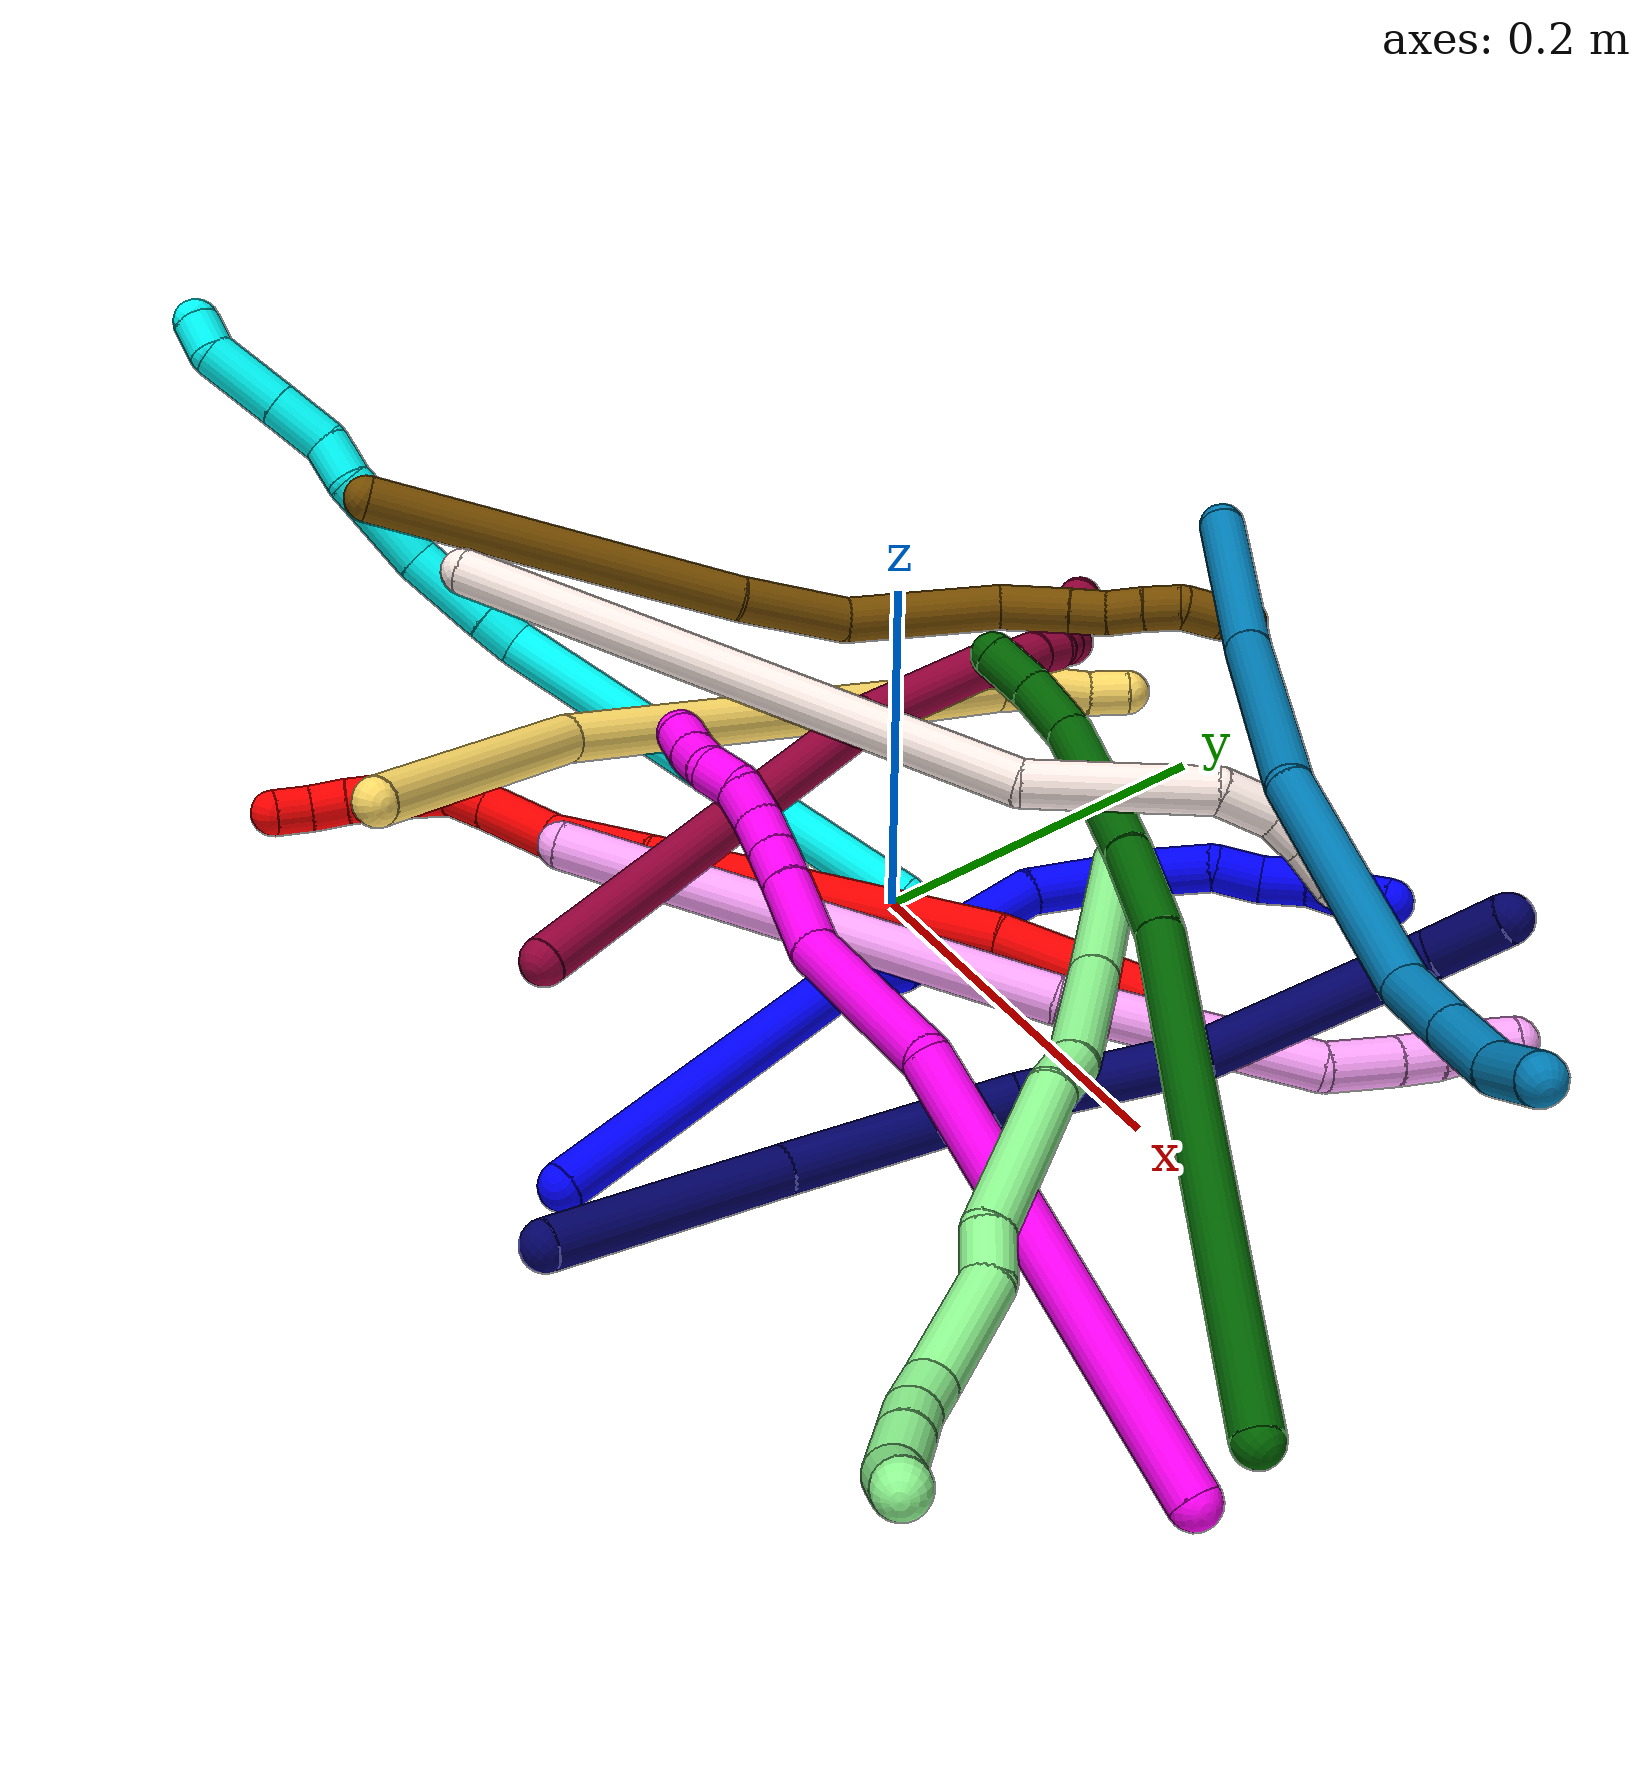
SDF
<sdf version="1.7">
 <world name="default">
  <plugin name="TubeGeneratorPlugin" filename="libtube_generator_plugin.so"/>
  <model name="photoneo_s_sensor">
   <static>1</static>
   <pose>0 0 2 1.57079 1.57079 3.14159</pose>
   <link name="link">
    <inertial><mass>0.1</mass></inertial>
    <sensor name="sensor" type="depth">
     <update_rate>30</update_rate>
     <camera>
      <horizontal_fov>1.22</horizontal_fov>
      <image><width>1920</width><height>1200</height><format>B8G8R8</format></image>
      <clip><near>0.1</near><far>4</far></clip>
      <depth_camera><output>points</output></depth_camera>
     </camera>
     <plugin name="camera_plugin" filename="libgazebo_ros_depth_camera.so">
      <baseline>0.2</baseline>
      <alwaysOn>1</alwaysOn>
      <updateRate>0.0</updateRate>
      <cameraName>camera_ir</cameraName>
      <imageTopicName>/camera/color/image_raw</imageTopicName>
      <cameraInfoTopicName>/camera/color/camera_info</cameraInfoTopicName>
      <depthImageTopicName>/camera/depth/image_raw</depthImageTopicName>
      <depthImageCameraInfoTopicName>/camera/depth/camera_info</depthImageCameraInfoTopicName>
      <pointCloudTopicName>/camera/depth/points</pointCloudTopicName>
      <frameName>fr_optical</frameName>
      <pointCloudCutoff>0.1</pointCloudCutoff>
      <pointCloudCutoffMax>2.0</pointCloudCutoffMax>
      <distortionK1>0</distortionK1>
      <distortionK2>0</distortionK2>
      <distortionK3>0</distortionK3>
      <distortionT1>0</distortionT1>
      <distortionT2>0</distortionT2>
      <CxPrime>0</CxPrime>
      <Cx>0</Cx>
      <Cy>0</Cy>
      <focalLength>0</focalLength>
      <hackBaseline>0</hackBaseline>
     </plugin>
    </sensor>
   </link>
  </model>
  <gravity>0 0 -9.8</gravity>
  <magnetic_field>6e-06 2.3e-05 -4.2e-05</magnetic_field>
  <atmosphere type="adiabatic"/>
  <physics name="default_physics" default="0" type="ode">
   <max_step_size>0.003</max_step_size>
   <real_time_factor>1</real_time_factor>
   <real_time_update_rate>1000</real_time_update_rate>
   <max_contacts>10000</max_contacts>
   <ode>
    <solver>
     <type>quick</type>
     <iters>100</iters>
     <sor>1.3</sor>
     <use_dynamic_moi_rescaling>0</use_dynamic_moi_rescaling>
    </solver>
    <constraints>
     <contact_max_correcting_vel>0</contact_max_correcting_vel>
     <contact_surface_layer>0.001</contact_surface_layer>
     <cfm>0</cfm>
     <erp>0.2</erp>
    </constraints>
   </ode>
  </physics>
  <scene><ambient>0.4 0.4 0.4 1</ambient><background>0.7 0.7 0.7 1</background><shadows>0</shadows></scene>
  <audio><device>default</device></audio>
  <spherical_coordinates>
   <surface_model>EARTH_WGS84</surface_model>
   <latitude_deg>0</latitude_deg>
   <longitude_deg>0</longitude_deg>
   <elevation>0</elevation>
   <heading_deg>0</heading_deg>
  </spherical_coordinates>
  <model name="bin">
   <static>1</static>
   <link name="bottom">
    <collision name="collision-bottom">
     <pose>0 0 -0.01 0 -0 0</pose>
     <geometry><box><size>0.8 0.6 0.02</size></box></geometry>
     <surface>
      <friction><ode><mu>100</mu><mu2>100</mu2></ode></friction>
      <contact><collide_bitmask>65535</collide_bitmask></contact>
     </surface>
    </collision>
   </link>
   <link name="west_wall">
    <collision name="collision-west_wall">
     <pose>-0.41 0 0.1 0 -0 0</pose>
     <geometry><box><size>0.02 0.6 0.2</size></box></geometry>
     <surface>
      <friction><ode><mu>100</mu><mu2>100</mu2></ode></friction>
      <contact><collide_bitmask>65535</collide_bitmask></contact>
     </surface>
    </collision>
   </link>
   <link name="east_wall">
    <collision name="collision-east_wall">
     <pose>0.41 0 0.1 0 -0 0</pose>
     <geometry><box><size>0.02 0.6 0.2</size></box></geometry>
     <surface>
      <friction><ode><mu>100</mu><mu2>100</mu2></ode></friction>
      <contact><collide_bitmask>65535</collide_bitmask></contact>
     </surface>
    </collision>
   </link>
   <link name="south_wall">
    <collision name="collision-south_wall">
     <pose>0 -0.31 0.1 0 -0 0</pose>
     <geometry><box><size>0.8 0.02 0.2</size></box></geometry>
     <surface>
      <friction><ode><mu>100</mu><mu2>100</mu2></ode></friction>
      <contact><collide_bitmask>65535</collide_bitmask></contact>
     </surface>
    </collision>
   </link>
   <link name="north_wall">
    <collision name="collision-north_wall">
     <pose>0 0.31 0.1 0 -0 0</pose>
     <geometry><box><size>0.8 0.02 0.2</size></box></geometry>
     <surface>
      <friction><ode><mu>100</mu><mu2>100</mu2></ode></friction>
      <contact><collide_bitmask>65535</collide_bitmask></contact>
     </surface>
    </collision>
   </link>
  </model>
  <model name="1">
   <static>0</static>
   <link name="1">
    <collision name="collision-cylinder-e_1_1_4">
     <pose>-0.015159 0.083922 -0.032867 -1.94407 -0.166632 0.24357</pose>
     <geometry><cylinder><radius>0.0125</radius><length>0.182788</length></cylinder></geometry>
     <surface>
      <friction><ode><mu>1.16</mu><mu2>1.16</mu2><slip1>0</slip1><slip2>0</slip2></ode></friction>
      <contact><ode><kp>1e+06</kp><kd>1</kd><max_vel>0</max_vel><min_depth>0.001</min_depth></ode></contact>
     </surface>
    </collision>
    <visual name="visual-cylinder-e_1_1_4">
     <pose>-0.015159 0.083922 -0.032867 -1.94407 -0.166632 0.24357</pose>
     <geometry><cylinder><radius>0.0125</radius><length>0.182788</length></cylinder></geometry>
     <material><ambient>0 0 1 1</ambient></material>
    </visual>
    <collision name="collision-cylinder-e_2_4_5">
     <pose>-0.029714 0.182737 -0.07765 -2.2456 0.031616 -0.065768</pose>
     <geometry><cylinder><radius>0.0125</radius><length>0.038167</length></cylinder></geometry>
     <surface>
      <friction><ode><mu>1.16</mu><mu2>1.16</mu2><slip1>0</slip1><slip2>0</slip2></ode></friction>
      <contact><ode><kp>1e+06</kp><kd>1</kd><max_vel>0</max_vel><min_depth>0.001</min_depth></ode></contact>
     </surface>
    </collision>
    <visual name="visual-cylinder-e_2_4_5">
     <pose>-0.029714 0.182737 -0.07765 -2.2456 0.031616 -0.065768</pose>
     <geometry><cylinder><radius>0.0125</radius><length>0.038167</length></cylinder></geometry>
     <material><ambient>0 0 1 1</ambient></material>
    </visual>
    <collision name="collision-cylinder-e_3_5_6">
     <pose>-0.031907 0.238053 -0.10512 -1.93812 -0.064472 0.093852</pose>
     <geometry><cylinder><radius>0.0125</radius><length>0.086805</length></cylinder></geometry>
     <surface>
      <friction><ode><mu>1.16</mu><mu2>1.16</mu2><slip1>0</slip1><slip2>0</slip2></ode></friction>
      <contact><ode><kp>1e+06</kp><kd>1</kd><max_vel>0</max_vel><min_depth>0.001</min_depth></ode></contact>
     </surface>
    </collision>
    <visual name="visual-cylinder-e_3_5_6">
     <pose>-0.031907 0.238053 -0.10512 -1.93812 -0.064472 0.093852</pose>
     <geometry><cylinder><radius>0.0125</radius><length>0.086805</length></cylinder></geometry>
     <material><ambient>0 0 1 1</ambient></material>
    </visual>
    <collision name="collision-cylinder-e_4_6_7">
     <pose>-0.022903 0.3062 -0.129959 -1.89395 0.383628 -0.527122</pose>
     <geometry><cylinder><radius>0.0125</radius><length>0.063057</length></cylinder></geometry>
     <surface>
      <friction><ode><mu>1.16</mu><mu2>1.16</mu2><slip1>0</slip1><slip2>0</slip2></ode></friction>
      <contact><ode><kp>1e+06</kp><kd>1</kd><max_vel>0</max_vel><min_depth>0.001</min_depth></ode></contact>
     </surface>
    </collision>
    <visual name="visual-cylinder-e_4_6_7">
     <pose>-0.022903 0.3062 -0.129959 -1.89395 0.383628 -0.527122</pose>
     <geometry><cylinder><radius>0.0125</radius><length>0.063057</length></cylinder></geometry>
     <material><ambient>0 0 1 1</ambient></material>
    </visual>
    <collision name="collision-cylinder-e_5_7_8">
     <pose>0.0009 0.34742 -0.137304 -1.42812 0.721802 -0.632237</pose>
     <geometry><cylinder><radius>0.0125</radius><length>0.03633</length></cylinder></geometry>
     <surface>
      <friction><ode><mu>1.16</mu><mu2>1.16</mu2><slip1>0</slip1><slip2>0</slip2></ode></friction>
      <contact><ode><kp>1e+06</kp><kd>1</kd><max_vel>0</max_vel><min_depth>0.001</min_depth></ode></contact>
     </surface>
    </collision>
    <visual name="visual-cylinder-e_5_7_8">
     <pose>0.0009 0.34742 -0.137304 -1.42812 0.721802 -0.632237</pose>
     <geometry><cylinder><radius>0.0125</radius><length>0.03633</length></cylinder></geometry>
     <material><ambient>0 0 1 1</ambient></material>
    </visual>
    <collision name="collision-cylinder-e_6_8_9">
     <pose>0.022073 0.368589 -0.139375 -2.05233 0.814186 -1.23723</pose>
     <geometry><cylinder><radius>0.0125</radius><length>0.025222</length></cylinder></geometry>
     <surface>
      <friction><ode><mu>1.16</mu><mu2>1.16</mu2><slip1>0</slip1><slip2>0</slip2></ode></friction>
      <contact><ode><kp>1e+06</kp><kd>1</kd><max_vel>0</max_vel><min_depth>0.001</min_depth></ode></contact>
     </surface>
    </collision>
    <visual name="visual-cylinder-e_6_8_9">
     <pose>0.022073 0.368589 -0.139375 -2.05233 0.814186 -1.23723</pose>
     <geometry><cylinder><radius>0.0125</radius><length>0.025222</length></cylinder></geometry>
     <material><ambient>0 0 1 1</ambient></material>
    </visual>
    <collision name="collision-cylinder-e_7_9_10">
     <pose>0.04084 0.384607 -0.142641 -1.482 0.853059 -0.788049</pose>
     <geometry><cylinder><radius>0.0125</radius><length>0.025478</length></cylinder></geometry>
     <surface>
      <friction><ode><mu>1.16</mu><mu2>1.16</mu2><slip1>0</slip1><slip2>0</slip2></ode></friction>
      <contact><ode><kp>1e+06</kp><kd>1</kd><max_vel>0</max_vel><min_depth>0.001</min_depth></ode></contact>
     </surface>
    </collision>
    <visual name="visual-cylinder-e_7_9_10">
     <pose>0.04084 0.384607 -0.142641 -1.482 0.853059 -0.788049</pose>
     <geometry><cylinder><radius>0.0125</radius><length>0.025478</length></cylinder></geometry>
     <material><ambient>0 0 1 1</ambient></material>
    </visual>
    <collision name="collision-cylinder-e_8_10_11">
     <pose>0.059651 0.398667 -0.143937 -1.91347 0.988488 -1.30524</pose>
     <geometry><cylinder><radius>0.0125</radius><length>0.022066</length></cylinder></geometry>
     <surface>
      <friction><ode><mu>1.16</mu><mu2>1.16</mu2><slip1>0</slip1><slip2>0</slip2></ode></friction>
      <contact><ode><kp>1e+06</kp><kd>1</kd><max_vel>0</max_vel><min_depth>0.001</min_depth></ode></contact>
     </surface>
    </collision>
    <visual name="visual-cylinder-e_8_10_11">
     <pose>0.059651 0.398667 -0.143937 -1.91347 0.988488 -1.30524</pose>
     <geometry><cylinder><radius>0.0125</radius><length>0.022066</length></cylinder></geometry>
     <material><ambient>0 0 1 1</ambient></material>
    </visual>
    <collision name="collision-cylinder-e_9_11_2">
     <pose>0.077206 0.409918 -0.145167 -1.42577 0.979894 -0.864067</pose>
     <geometry><cylinder><radius>0.0125</radius><length>0.020086</length></cylinder></geometry>
     <surface>
      <friction><ode><mu>1.16</mu><mu2>1.16</mu2><slip1>0</slip1><slip2>0</slip2></ode></friction>
      <contact><ode><kp>1e+06</kp><kd>1</kd><max_vel>0</max_vel><min_depth>0.001</min_depth></ode></contact>
     </surface>
    </collision>
    <visual name="visual-cylinder-e_9_11_2">
     <pose>0.077206 0.409918 -0.145167 -1.42577 0.979894 -0.864067</pose>
     <geometry><cylinder><radius>0.0125</radius><length>0.020086</length></cylinder></geometry>
     <material><ambient>0 0 1 1</ambient></material>
    </visual>
    <collision name="collision-sphere-2">
     <pose>0.085546 0.415455 -0.144359 0 -0 0</pose>
     <geometry><sphere><radius>0.0125</radius></sphere></geometry>
     <surface>
      <friction><ode><mu>1.16</mu><mu2>1.16</mu2><slip1>0</slip1><slip2>0</slip2></ode></friction>
      <contact><ode><kp>1e+06</kp><kd>1</kd><max_vel>0</max_vel><min_depth>0.001</min_depth></ode></contact>
     </surface>
    </collision>
    <visual name="visual-sphere-2">
     <pose>0.085546 0.415455 -0.144359 0 -0 0</pose>
     <geometry><sphere><radius>0.0125</radius></sphere></geometry>
     <material><ambient>0 0 1 1</ambient></material>
    </visual>
    <collision name="collision-sphere-11">
     <pose>0.068866 0.404382 -0.145976 0 -0 0</pose>
     <geometry><sphere><radius>0.0125</radius></sphere></geometry>
     <surface>
      <friction><ode><mu>1.16</mu><mu2>1.16</mu2><slip1>0</slip1><slip2>0</slip2></ode></friction>
      <contact><ode><kp>1e+06</kp><kd>1</kd><max_vel>0</max_vel><min_depth>0.001</min_depth></ode></contact>
     </surface>
    </collision>
    <visual name="visual-sphere-11">
     <pose>0.068866 0.404382 -0.145976 0 -0 0</pose>
     <geometry><sphere><radius>0.0125</radius></sphere></geometry>
     <material><ambient>0 0 1 1</ambient></material>
    </visual>
    <collision name="collision-sphere-10">
     <pose>0.050436 0.392952 -0.141898 0 -0 0</pose>
     <geometry><sphere><radius>0.0125</radius></sphere></geometry>
     <surface>
      <friction><ode><mu>1.16</mu><mu2>1.16</mu2><slip1>0</slip1><slip2>0</slip2></ode></friction>
      <contact><ode><kp>1e+06</kp><kd>1</kd><max_vel>0</max_vel><min_depth>0.001</min_depth></ode></contact>
     </surface>
    </collision>
    <visual name="visual-sphere-10">
     <pose>0.050436 0.392952 -0.141898 0 -0 0</pose>
     <geometry><sphere><radius>0.0125</radius></sphere></geometry>
     <material><ambient>0 0 1 1</ambient></material>
    </visual>
    <collision name="collision-sphere-9">
     <pose>0.031243 0.376261 -0.143384 0 -0 0</pose>
     <geometry><sphere><radius>0.0125</radius></sphere></geometry>
     <surface>
      <friction><ode><mu>1.16</mu><mu2>1.16</mu2><slip1>0</slip1><slip2>0</slip2></ode></friction>
      <contact><ode><kp>1e+06</kp><kd>1</kd><max_vel>0</max_vel><min_depth>0.001</min_depth></ode></contact>
     </surface>
    </collision>
    <visual name="visual-sphere-9">
     <pose>0.031243 0.376261 -0.143384 0 -0 0</pose>
     <geometry><sphere><radius>0.0125</radius></sphere></geometry>
     <material><ambient>0 0 1 1</ambient></material>
    </visual>
    <collision name="collision-sphere-4">
     <pose>-0.030318 0.167843 -0.065734 0 -0 0</pose>
     <geometry><sphere><radius>0.0125</radius></sphere></geometry>
     <surface>
      <friction><ode><mu>1.16</mu><mu2>1.16</mu2><slip1>0</slip1><slip2>0</slip2></ode></friction>
      <contact><ode><kp>1e+06</kp><kd>1</kd><max_vel>0</max_vel><min_depth>0.001</min_depth></ode></contact>
     </surface>
    </collision>
    <visual name="visual-sphere-4">
     <pose>-0.030318 0.167843 -0.065734 0 -0 0</pose>
     <geometry><sphere><radius>0.0125</radius></sphere></geometry>
     <material><ambient>0 0 1 1</ambient></material>
    </visual>
    <collision name="collision-sphere-1">
     <geometry><sphere><radius>0.0125</radius></sphere></geometry>
     <surface>
      <friction><ode><mu>1.16</mu><mu2>1.16</mu2><slip1>0</slip1><slip2>0</slip2></ode></friction>
      <contact><ode><kp>1e+06</kp><kd>1</kd><max_vel>0</max_vel><min_depth>0.001</min_depth></ode></contact>
     </surface>
    </collision>
    <visual name="visual-sphere-1">
     <geometry><sphere><radius>0.0125</radius></sphere></geometry>
     <material><ambient>0 0 1 1</ambient></material>
    </visual>
    <collision name="collision-sphere-8">
     <pose>0.012902 0.360916 -0.135365 0 -0 0</pose>
     <geometry><sphere><radius>0.0125</radius></sphere></geometry>
     <surface>
      <friction><ode><mu>1.16</mu><mu2>1.16</mu2><slip1>0</slip1><slip2>0</slip2></ode></friction>
      <contact><ode><kp>1e+06</kp><kd>1</kd><max_vel>0</max_vel><min_depth>0.001</min_depth></ode></contact>
     </surface>
    </collision>
    <visual name="visual-sphere-8">
     <pose>0.012902 0.360916 -0.135365 0 -0 0</pose>
     <geometry><sphere><radius>0.0125</radius></sphere></geometry>
     <material><ambient>0 0 1 1</ambient></material>
    </visual>
    <collision name="collision-sphere-5">
     <pose>-0.029111 0.19763 -0.089566 0 -0 0</pose>
     <geometry><sphere><radius>0.0125</radius></sphere></geometry>
     <surface>
      <friction><ode><mu>1.16</mu><mu2>1.16</mu2><slip1>0</slip1><slip2>0</slip2></ode></friction>
      <contact><ode><kp>1e+06</kp><kd>1</kd><max_vel>0</max_vel><min_depth>0.001</min_depth></ode></contact>
     </surface>
    </collision>
    <visual name="visual-sphere-5">
     <pose>-0.029111 0.19763 -0.089566 0 -0 0</pose>
     <geometry><sphere><radius>0.0125</radius></sphere></geometry>
     <material><ambient>0 0 1 1</ambient></material>
    </visual>
    <collision name="collision-sphere-6">
     <pose>-0.034704 0.278476 -0.120674 0 -0 0</pose>
     <geometry><sphere><radius>0.0125</radius></sphere></geometry>
     <surface>
      <friction><ode><mu>1.16</mu><mu2>1.16</mu2><slip1>0</slip1><slip2>0</slip2></ode></friction>
      <contact><ode><kp>1e+06</kp><kd>1</kd><max_vel>0</max_vel><min_depth>0.001</min_depth></ode></contact>
     </surface>
    </collision>
    <visual name="visual-sphere-6">
     <pose>-0.034704 0.278476 -0.120674 0 -0 0</pose>
     <geometry><sphere><radius>0.0125</radius></sphere></geometry>
     <material><ambient>0 0 1 1</ambient></material>
    </visual>
    <collision name="collision-sphere-7">
     <pose>-0.011102 0.333923 -0.139243 0 -0 0</pose>
     <geometry><sphere><radius>0.0125</radius></sphere></geometry>
     <surface>
      <friction><ode><mu>1.16</mu><mu2>1.16</mu2><slip1>0</slip1><slip2>0</slip2></ode></friction>
      <contact><ode><kp>1e+06</kp><kd>1</kd><max_vel>0</max_vel><min_depth>0.001</min_depth></ode></contact>
     </surface>
    </collision>
    <visual name="visual-sphere-7">
     <pose>-0.011102 0.333923 -0.139243 0 -0 0</pose>
     <geometry><sphere><radius>0.0125</radius></sphere></geometry>
     <material><ambient>0 0 1 1</ambient></material>
    </visual>
    <inertial>
     <pose>-0.007244 0.22207 -0.089042 0 -0 0</pose>
     <mass>0.5</mass>
     <inertia>
      <ixx>0.000699</ixx>
      <ixy>0</ixy>
      <ixz>0</ixz>
      <iyy>-4e-05</iyy>
      <iyz>0</iyz>
      <izz>-0.000502</izz>
     </inertia>
    </inertial>
   </link>
   <pose>0.082244 -0.250623 0.011897 0.402543 0.155435 0.001176</pose>
  </model>
  <model name="2">
   <static>0</static>
   <link name="2">
    <collision name="collision-cylinder-e_1_1_4">
     <pose>-0.014691 -0.006811 0.038754 0.173969 -0.357338 -0.031495</pose>
     <geometry><cylinder><radius>0.0125</radius><length>0.084002</length></cylinder></geometry>
     <surface>
      <friction><ode><mu>1.16</mu><mu2>1.16</mu2><slip1>0</slip1><slip2>0</slip2></ode></friction>
      <contact><ode><kp>1e+06</kp><kd>1</kd><max_vel>0</max_vel><min_depth>0.001</min_depth></ode></contact>
     </surface>
    </collision>
    <visual name="visual-cylinder-e_1_1_4">
     <pose>-0.014691 -0.006811 0.038754 0.173969 -0.357338 -0.031495</pose>
     <geometry><cylinder><radius>0.0125</radius><length>0.084002</length></cylinder></geometry>
     <material><ambient>1 0 0 1</ambient></material>
    </visual>
    <collision name="collision-cylinder-e_2_4_5">
     <pose>-0.060978 -0.015496 0.165579 0.021279 -0.344373 -0.003701</pose>
     <geometry><cylinder><radius>0.0125</radius><length>0.187172</length></cylinder></geometry>
     <surface>
      <friction><ode><mu>1.16</mu><mu2>1.16</mu2><slip1>0</slip1><slip2>0</slip2></ode></friction>
      <contact><ode><kp>1e+06</kp><kd>1</kd><max_vel>0</max_vel><min_depth>0.001</min_depth></ode></contact>
     </surface>
    </collision>
    <visual name="visual-cylinder-e_2_4_5">
     <pose>-0.060978 -0.015496 0.165579 0.021279 -0.344373 -0.003701</pose>
     <geometry><cylinder><radius>0.0125</radius><length>0.187172</length></cylinder></geometry>
     <material><ambient>1 0 0 1</ambient></material>
    </visual>
    <collision name="collision-cylinder-e_3_5_6">
     <pose>-0.096614 -0.016559 0.283581 -0.02711 -0.134152 0.001821</pose>
     <geometry><cylinder><radius>0.0125</radius><length>0.060426</length></cylinder></geometry>
     <surface>
      <friction><ode><mu>1.16</mu><mu2>1.16</mu2><slip1>0</slip1><slip2>0</slip2></ode></friction>
      <contact><ode><kp>1e+06</kp><kd>1</kd><max_vel>0</max_vel><min_depth>0.001</min_depth></ode></contact>
     </surface>
    </collision>
    <visual name="visual-cylinder-e_3_5_6">
     <pose>-0.096614 -0.016559 0.283581 -0.02711 -0.134152 0.001821</pose>
     <geometry><cylinder><radius>0.0125</radius><length>0.060426</length></cylinder></geometry>
     <material><ambient>1 0 0 1</ambient></material>
    </visual>
    <collision name="collision-cylinder-e_4_6_7">
     <pose>-0.102961 -0.019181 0.334794 0.15997 -0.106595 -0.008552</pose>
     <geometry><cylinder><radius>0.0125</radius><length>0.043361</length></cylinder></geometry>
     <surface>
      <friction><ode><mu>1.16</mu><mu2>1.16</mu2><slip1>0</slip1><slip2>0</slip2></ode></friction>
      <contact><ode><kp>1e+06</kp><kd>1</kd><max_vel>0</max_vel><min_depth>0.001</min_depth></ode></contact>
     </surface>
    </collision>
    <visual name="visual-cylinder-e_4_6_7">
     <pose>-0.102961 -0.019181 0.334794 0.15997 -0.106595 -0.008552</pose>
     <geometry><cylinder><radius>0.0125</radius><length>0.043361</length></cylinder></geometry>
     <material><ambient>1 0 0 1</ambient></material>
    </visual>
    <collision name="collision-cylinder-e_5_7_8">
     <pose>-0.107765 -0.024435 0.368008 0.151357 -0.204012 -0.015522</pose>
     <geometry><cylinder><radius>0.0125</radius><length>0.024652</length></cylinder></geometry>
     <surface>
      <friction><ode><mu>1.16</mu><mu2>1.16</mu2><slip1>0</slip1><slip2>0</slip2></ode></friction>
      <contact><ode><kp>1e+06</kp><kd>1</kd><max_vel>0</max_vel><min_depth>0.001</min_depth></ode></contact>
     </surface>
    </collision>
    <visual name="visual-cylinder-e_5_7_8">
     <pose>-0.107765 -0.024435 0.368008 0.151357 -0.204012 -0.015522</pose>
     <geometry><cylinder><radius>0.0125</radius><length>0.024652</length></cylinder></geometry>
     <material><ambient>1 0 0 1</ambient></material>
    </visual>
    <collision name="collision-cylinder-e_6_8_9">
     <pose>-0.112584 -0.02382 0.389413 -0.251593 -0.233057 0.029605</pose>
     <geometry><cylinder><radius>0.0125</radius><length>0.020103</length></cylinder></geometry>
     <surface>
      <friction><ode><mu>1.16</mu><mu2>1.16</mu2><slip1>0</slip1><slip2>0</slip2></ode></friction>
      <contact><ode><kp>1e+06</kp><kd>1</kd><max_vel>0</max_vel><min_depth>0.001</min_depth></ode></contact>
     </surface>
    </collision>
    <visual name="visual-cylinder-e_6_8_9">
     <pose>-0.112584 -0.02382 0.389413 -0.251593 -0.233057 0.029605</pose>
     <geometry><cylinder><radius>0.0125</radius><length>0.020103</length></cylinder></geometry>
     <material><ambient>1 0 0 1</ambient></material>
    </visual>
    <collision name="collision-cylinder-e_7_9_10">
     <pose>-0.1181 -0.018755 0.408131 -0.277185 -0.320874 0.045138</pose>
     <geometry><cylinder><radius>0.0125</radius><length>0.02026</length></cylinder></geometry>
     <surface>
      <friction><ode><mu>1.16</mu><mu2>1.16</mu2><slip1>0</slip1><slip2>0</slip2></ode></friction>
      <contact><ode><kp>1e+06</kp><kd>1</kd><max_vel>0</max_vel><min_depth>0.001</min_depth></ode></contact>
     </surface>
    </collision>
    <visual name="visual-cylinder-e_7_9_10">
     <pose>-0.1181 -0.018755 0.408131 -0.277185 -0.320874 0.045138</pose>
     <geometry><cylinder><radius>0.0125</radius><length>0.02026</length></cylinder></geometry>
     <material><ambient>1 0 0 1</ambient></material>
    </visual>
    <collision name="collision-cylinder-e_8_10_11">
     <pose>-0.127855 -0.013611 0.424507 -0.338933 -0.714655 0.127594</pose>
     <geometry><cylinder><radius>0.0125</radius><length>0.020018</length></cylinder></geometry>
     <surface>
      <friction><ode><mu>1.16</mu><mu2>1.16</mu2><slip1>0</slip1><slip2>0</slip2></ode></friction>
      <contact><ode><kp>1e+06</kp><kd>1</kd><max_vel>0</max_vel><min_depth>0.001</min_depth></ode></contact>
     </surface>
    </collision>
    <visual name="visual-cylinder-e_8_10_11">
     <pose>-0.127855 -0.013611 0.424507 -0.338933 -0.714655 0.127594</pose>
     <geometry><cylinder><radius>0.0125</radius><length>0.020018</length></cylinder></geometry>
     <material><ambient>1 0 0 1</ambient></material>
    </visual>
    <collision name="collision-cylinder-e_9_11_12">
     <pose>-0.140936 -0.007852 0.43849 -0.442246 -0.710279 0.166355</pose>
     <geometry><cylinder><radius>0.0125</radius><length>0.020004</length></cylinder></geometry>
     <surface>
      <friction><ode><mu>1.16</mu><mu2>1.16</mu2><slip1>0</slip1><slip2>0</slip2></ode></friction>
      <contact><ode><kp>1e+06</kp><kd>1</kd><max_vel>0</max_vel><min_depth>0.001</min_depth></ode></contact>
     </surface>
    </collision>
    <visual name="visual-cylinder-e_9_11_12">
     <pose>-0.140936 -0.007852 0.43849 -0.442246 -0.710279 0.166355</pose>
     <geometry><cylinder><radius>0.0125</radius><length>0.020004</length></cylinder></geometry>
     <material><ambient>1 0 0 1</ambient></material>
    </visual>
    <collision name="collision-cylinder-e_10_12_2">
     <pose>-0.155645 -0.002509 0.450691 -0.373723 -0.959052 0.196003</pose>
     <geometry><cylinder><radius>0.0125</radius><length>0.020002</length></cylinder></geometry>
     <surface>
      <friction><ode><mu>1.16</mu><mu2>1.16</mu2><slip1>0</slip1><slip2>0</slip2></ode></friction>
      <contact><ode><kp>1e+06</kp><kd>1</kd><max_vel>0</max_vel><min_depth>0.001</min_depth></ode></contact>
     </surface>
    </collision>
    <visual name="visual-cylinder-e_10_12_2">
     <pose>-0.155645 -0.002509 0.450691 -0.373723 -0.959052 0.196003</pose>
     <geometry><cylinder><radius>0.0125</radius><length>0.020002</length></cylinder></geometry>
     <material><ambient>1 0 0 1</ambient></material>
    </visual>
    <collision name="collision-sphere-2">
     <pose>-0.163832 -0.000413 0.456038 0 -0 0</pose>
     <geometry><sphere><radius>0.0125</radius></sphere></geometry>
     <surface>
      <friction><ode><mu>1.16</mu><mu2>1.16</mu2><slip1>0</slip1><slip2>0</slip2></ode></friction>
      <contact><ode><kp>1e+06</kp><kd>1</kd><max_vel>0</max_vel><min_depth>0.001</min_depth></ode></contact>
     </surface>
    </collision>
    <visual name="visual-sphere-2">
     <pose>-0.163832 -0.000413 0.456038 0 -0 0</pose>
     <geometry><sphere><radius>0.0125</radius></sphere></geometry>
     <material><ambient>1 0 0 1</ambient></material>
    </visual>
    <collision name="collision-sphere-12">
     <pose>-0.147458 -0.004606 0.445344 0 -0 0</pose>
     <geometry><sphere><radius>0.0125</radius></sphere></geometry>
     <surface>
      <friction><ode><mu>1.16</mu><mu2>1.16</mu2><slip1>0</slip1><slip2>0</slip2></ode></friction>
      <contact><ode><kp>1e+06</kp><kd>1</kd><max_vel>0</max_vel><min_depth>0.001</min_depth></ode></contact>
     </surface>
    </collision>
    <visual name="visual-sphere-12">
     <pose>-0.147458 -0.004606 0.445344 0 -0 0</pose>
     <geometry><sphere><radius>0.0125</radius></sphere></geometry>
     <material><ambient>1 0 0 1</ambient></material>
    </visual>
    <collision name="collision-sphere-11">
     <pose>-0.134414 -0.011097 0.431636 0 -0 0</pose>
     <geometry><sphere><radius>0.0125</radius></sphere></geometry>
     <surface>
      <friction><ode><mu>1.16</mu><mu2>1.16</mu2><slip1>0</slip1><slip2>0</slip2></ode></friction>
      <contact><ode><kp>1e+06</kp><kd>1</kd><max_vel>0</max_vel><min_depth>0.001</min_depth></ode></contact>
     </surface>
    </collision>
    <visual name="visual-sphere-11">
     <pose>-0.134414 -0.011097 0.431636 0 -0 0</pose>
     <geometry><sphere><radius>0.0125</radius></sphere></geometry>
     <material><ambient>1 0 0 1</ambient></material>
    </visual>
    <collision name="collision-sphere-10">
     <pose>-0.121295 -0.016124 0.417377 0 -0 0</pose>
     <geometry><sphere><radius>0.0125</radius></sphere></geometry>
     <surface>
      <friction><ode><mu>1.16</mu><mu2>1.16</mu2><slip1>0</slip1><slip2>0</slip2></ode></friction>
      <contact><ode><kp>1e+06</kp><kd>1</kd><max_vel>0</max_vel><min_depth>0.001</min_depth></ode></contact>
     </surface>
    </collision>
    <visual name="visual-sphere-10">
     <pose>-0.121295 -0.016124 0.417377 0 -0 0</pose>
     <geometry><sphere><radius>0.0125</radius></sphere></geometry>
     <material><ambient>1 0 0 1</ambient></material>
    </visual>
    <collision name="collision-sphere-9">
     <pose>-0.114906 -0.021385 0.398885 0 -0 0</pose>
     <geometry><sphere><radius>0.0125</radius></sphere></geometry>
     <surface>
      <friction><ode><mu>1.16</mu><mu2>1.16</mu2><slip1>0</slip1><slip2>0</slip2></ode></friction>
      <contact><ode><kp>1e+06</kp><kd>1</kd><max_vel>0</max_vel><min_depth>0.001</min_depth></ode></contact>
     </surface>
    </collision>
    <visual name="visual-sphere-9">
     <pose>-0.114906 -0.021385 0.398885 0 -0 0</pose>
     <geometry><sphere><radius>0.0125</radius></sphere></geometry>
     <material><ambient>1 0 0 1</ambient></material>
    </visual>
    <collision name="collision-sphere-4">
     <pose>-0.029382 -0.013622 0.077508 0 -0 0</pose>
     <geometry><sphere><radius>0.0125</radius></sphere></geometry>
     <surface>
      <friction><ode><mu>1.16</mu><mu2>1.16</mu2><slip1>0</slip1><slip2>0</slip2></ode></friction>
      <contact><ode><kp>1e+06</kp><kd>1</kd><max_vel>0</max_vel><min_depth>0.001</min_depth></ode></contact>
     </surface>
    </collision>
    <visual name="visual-sphere-4">
     <pose>-0.029382 -0.013622 0.077508 0 -0 0</pose>
     <geometry><sphere><radius>0.0125</radius></sphere></geometry>
     <material><ambient>1 0 0 1</ambient></material>
    </visual>
    <collision name="collision-sphere-1">
     <geometry><sphere><radius>0.0125</radius></sphere></geometry>
     <surface>
      <friction><ode><mu>1.16</mu><mu2>1.16</mu2><slip1>0</slip1><slip2>0</slip2></ode></friction>
      <contact><ode><kp>1e+06</kp><kd>1</kd><max_vel>0</max_vel><min_depth>0.001</min_depth></ode></contact>
     </surface>
    </collision>
    <visual name="visual-sphere-1">
     <geometry><sphere><radius>0.0125</radius></sphere></geometry>
     <material><ambient>1 0 0 1</ambient></material>
    </visual>
    <collision name="collision-sphere-8">
     <pose>-0.110263 -0.026255 0.379941 0 -0 0</pose>
     <geometry><sphere><radius>0.0125</radius></sphere></geometry>
     <surface>
      <friction><ode><mu>1.16</mu><mu2>1.16</mu2><slip1>0</slip1><slip2>0</slip2></ode></friction>
      <contact><ode><kp>1e+06</kp><kd>1</kd><max_vel>0</max_vel><min_depth>0.001</min_depth></ode></contact>
     </surface>
    </collision>
    <visual name="visual-sphere-8">
     <pose>-0.110263 -0.026255 0.379941 0 -0 0</pose>
     <geometry><sphere><radius>0.0125</radius></sphere></geometry>
     <material><ambient>1 0 0 1</ambient></material>
    </visual>
    <collision name="collision-sphere-5">
     <pose>-0.092573 -0.01737 0.25365 0 -0 0</pose>
     <geometry><sphere><radius>0.0125</radius></sphere></geometry>
     <surface>
      <friction><ode><mu>1.16</mu><mu2>1.16</mu2><slip1>0</slip1><slip2>0</slip2></ode></friction>
      <contact><ode><kp>1e+06</kp><kd>1</kd><max_vel>0</max_vel><min_depth>0.001</min_depth></ode></contact>
     </surface>
    </collision>
    <visual name="visual-sphere-5">
     <pose>-0.092573 -0.01737 0.25365 0 -0 0</pose>
     <geometry><sphere><radius>0.0125</radius></sphere></geometry>
     <material><ambient>1 0 0 1</ambient></material>
    </visual>
    <collision name="collision-sphere-6">
     <pose>-0.100655 -0.015747 0.313512 0 -0 0</pose>
     <geometry><sphere><radius>0.0125</radius></sphere></geometry>
     <surface>
      <friction><ode><mu>1.16</mu><mu2>1.16</mu2><slip1>0</slip1><slip2>0</slip2></ode></friction>
      <contact><ode><kp>1e+06</kp><kd>1</kd><max_vel>0</max_vel><min_depth>0.001</min_depth></ode></contact>
     </surface>
    </collision>
    <visual name="visual-sphere-6">
     <pose>-0.100655 -0.015747 0.313512 0 -0 0</pose>
     <geometry><sphere><radius>0.0125</radius></sphere></geometry>
     <material><ambient>1 0 0 1</ambient></material>
    </visual>
    <collision name="collision-sphere-7">
     <pose>-0.105268 -0.022615 0.356076 0 -0 0</pose>
     <geometry><sphere><radius>0.0125</radius></sphere></geometry>
     <surface>
      <friction><ode><mu>1.16</mu><mu2>1.16</mu2><slip1>0</slip1><slip2>0</slip2></ode></friction>
      <contact><ode><kp>1e+06</kp><kd>1</kd><max_vel>0</max_vel><min_depth>0.001</min_depth></ode></contact>
     </surface>
    </collision>
    <visual name="visual-sphere-7">
     <pose>-0.105268 -0.022615 0.356076 0 -0 0</pose>
     <geometry><sphere><radius>0.0125</radius></sphere></geometry>
     <material><ambient>1 0 0 1</ambient></material>
    </visual>
    <inertial>
     <pose>-0.077509 -0.014492 0.234706 0 -0 0</pose>
     <mass>0.5</mass>
     <inertia>
      <ixx>0.000592</ixx>
      <ixy>0</ixy>
      <ixz>0</ixz>
      <iyy>0.000641</iyy>
      <iyz>0</iyz>
      <izz>0.000268</izz>
     </inertia>
    </inertial>
   </link>
   <pose>0.154449 0.047677 0.026087 -1.80695 0.518367 1.78679</pose>
  </model>
  <model name="3">
   <static>0</static>
   <link name="3">
    <collision name="collision-cylinder-e_1_1_4">
     <pose>-0.005556 -0.011084 0.125995 0.087748 -0.043903 -0.001928</pose>
     <geometry><cylinder><radius>0.0125</radius><length>0.253207</length></cylinder></geometry>
     <surface>
      <friction><ode><mu>1.16</mu><mu2>1.16</mu2><slip1>0</slip1><slip2>0</slip2></ode></friction>
      <contact><ode><kp>1e+06</kp><kd>1</kd><max_vel>0</max_vel><min_depth>0.001</min_depth></ode></contact>
     </surface>
    </collision>
    <visual name="visual-cylinder-e_1_1_4">
     <pose>-0.005556 -0.011084 0.125995 0.087748 -0.043903 -0.001928</pose>
     <geometry><cylinder><radius>0.0125</radius><length>0.253207</length></cylinder></geometry>
     <material><ambient>0.003922 1 0.996078 1</ambient></material>
    </visual>
    <collision name="collision-cylinder-e_2_4_5">
     <pose>-0.011806 -0.020021 0.262543 -0.200759 -0.064314 0.00648</pose>
     <geometry><cylinder><radius>0.0125</radius><length>0.021583</length></cylinder></geometry>
     <surface>
      <friction><ode><mu>1.16</mu><mu2>1.16</mu2><slip1>0</slip1><slip2>0</slip2></ode></friction>
      <contact><ode><kp>1e+06</kp><kd>1</kd><max_vel>0</max_vel><min_depth>0.001</min_depth></ode></contact>
     </surface>
    </collision>
    <visual name="visual-cylinder-e_2_4_5">
     <pose>-0.011806 -0.020021 0.262543 -0.200759 -0.064314 0.00648</pose>
     <geometry><cylinder><radius>0.0125</radius><length>0.021583</length></cylinder></geometry>
     <material><ambient>0.003922 1 0.996078 1</ambient></material>
    </visual>
    <collision name="collision-cylinder-e_3_5_6">
     <pose>-0.014954 -0.01352 0.29679 -0.18172 -0.101504 0.009256</pose>
     <geometry><cylinder><radius>0.0125</radius><length>0.048431</length></cylinder></geometry>
     <surface>
      <friction><ode><mu>1.16</mu><mu2>1.16</mu2><slip1>0</slip1><slip2>0</slip2></ode></friction>
      <contact><ode><kp>1e+06</kp><kd>1</kd><max_vel>0</max_vel><min_depth>0.001</min_depth></ode></contact>
     </surface>
    </collision>
    <visual name="visual-cylinder-e_3_5_6">
     <pose>-0.014954 -0.01352 0.29679 -0.18172 -0.101504 0.009256</pose>
     <geometry><cylinder><radius>0.0125</radius><length>0.048431</length></cylinder></geometry>
     <material><ambient>0.003922 1 0.996078 1</ambient></material>
    </visual>
    <collision name="collision-cylinder-e_4_6_7">
     <pose>-0.023008 -0.000357 0.346001 -0.332392 -0.204579 0.034433</pose>
     <geometry><cylinder><radius>0.0125</radius><length>0.05514</length></cylinder></geometry>
     <surface>
      <friction><ode><mu>1.16</mu><mu2>1.16</mu2><slip1>0</slip1><slip2>0</slip2></ode></friction>
      <contact><ode><kp>1e+06</kp><kd>1</kd><max_vel>0</max_vel><min_depth>0.001</min_depth></ode></contact>
     </surface>
    </collision>
    <visual name="visual-cylinder-e_4_6_7">
     <pose>-0.023008 -0.000357 0.346001 -0.332392 -0.204579 0.034433</pose>
     <geometry><cylinder><radius>0.0125</radius><length>0.05514</length></cylinder></geometry>
     <material><ambient>0.003922 1 0.996078 1</ambient></material>
    </visual>
    <collision name="collision-cylinder-e_5_7_8">
     <pose>-0.033783 0.009658 0.382567 -0.108796 -0.43562 0.024101</pose>
     <geometry><cylinder><radius>0.0125</radius><length>0.02452</length></cylinder></geometry>
     <surface>
      <friction><ode><mu>1.16</mu><mu2>1.16</mu2><slip1>0</slip1><slip2>0</slip2></ode></friction>
      <contact><ode><kp>1e+06</kp><kd>1</kd><max_vel>0</max_vel><min_depth>0.001</min_depth></ode></contact>
     </surface>
    </collision>
    <visual name="visual-cylinder-e_5_7_8">
     <pose>-0.033783 0.009658 0.382567 -0.108796 -0.43562 0.024101</pose>
     <geometry><cylinder><radius>0.0125</radius><length>0.02452</length></cylinder></geometry>
     <material><ambient>0.003922 1 0.996078 1</ambient></material>
    </visual>
    <collision name="collision-cylinder-e_6_8_9">
     <pose>-0.039788 0.01418 0.409571 -0.204854 -0.051022 0.005246</pose>
     <geometry><cylinder><radius>0.0125</radius><length>0.032632</length></cylinder></geometry>
     <surface>
      <friction><ode><mu>1.16</mu><mu2>1.16</mu2><slip1>0</slip1><slip2>0</slip2></ode></friction>
      <contact><ode><kp>1e+06</kp><kd>1</kd><max_vel>0</max_vel><min_depth>0.001</min_depth></ode></contact>
     </surface>
    </collision>
    <visual name="visual-cylinder-e_6_8_9">
     <pose>-0.039788 0.01418 0.409571 -0.204854 -0.051022 0.005246</pose>
     <geometry><cylinder><radius>0.0125</radius><length>0.032632</length></cylinder></geometry>
     <material><ambient>0.003922 1 0.996078 1</ambient></material>
    </visual>
    <collision name="collision-cylinder-e_7_9_10">
     <pose>-0.041625 0.02166 0.447101 -0.190708 -0.045691 0.004371</pose>
     <geometry><cylinder><radius>0.0125</radius><length>0.043994</length></cylinder></geometry>
     <surface>
      <friction><ode><mu>1.16</mu><mu2>1.16</mu2><slip1>0</slip1><slip2>0</slip2></ode></friction>
      <contact><ode><kp>1e+06</kp><kd>1</kd><max_vel>0</max_vel><min_depth>0.001</min_depth></ode></contact>
     </surface>
    </collision>
    <visual name="visual-cylinder-e_7_9_10">
     <pose>-0.041625 0.02166 0.447101 -0.190708 -0.045691 0.004371</pose>
     <geometry><cylinder><radius>0.0125</radius><length>0.043994</length></cylinder></geometry>
     <material><ambient>0.003922 1 0.996078 1</ambient></material>
    </visual>
    <collision name="collision-cylinder-e_8_10_2">
     <pose>-0.047684 0.026006 0.477588 -0.020355 -0.515833 0.00537</pose>
     <geometry><cylinder><radius>0.0125</radius><length>0.020494</length></cylinder></geometry>
     <surface>
      <friction><ode><mu>1.16</mu><mu2>1.16</mu2><slip1>0</slip1><slip2>0</slip2></ode></friction>
      <contact><ode><kp>1e+06</kp><kd>1</kd><max_vel>0</max_vel><min_depth>0.001</min_depth></ode></contact>
     </surface>
    </collision>
    <visual name="visual-cylinder-e_8_10_2">
     <pose>-0.047684 0.026006 0.477588 -0.020355 -0.515833 0.00537</pose>
     <geometry><cylinder><radius>0.0125</radius><length>0.020494</length></cylinder></geometry>
     <material><ambient>0.003922 1 0.996078 1</ambient></material>
    </visual>
    <collision name="collision-sphere-2">
     <pose>-0.052738 0.026188 0.4865 0 -0 0</pose>
     <geometry><sphere><radius>0.0125</radius></sphere></geometry>
     <surface>
      <friction><ode><mu>1.16</mu><mu2>1.16</mu2><slip1>0</slip1><slip2>0</slip2></ode></friction>
      <contact><ode><kp>1e+06</kp><kd>1</kd><max_vel>0</max_vel><min_depth>0.001</min_depth></ode></contact>
     </surface>
    </collision>
    <visual name="visual-sphere-2">
     <pose>-0.052738 0.026188 0.4865 0 -0 0</pose>
     <geometry><sphere><radius>0.0125</radius></sphere></geometry>
     <material><ambient>0.003922 1 0.996078 1</ambient></material>
    </visual>
    <collision name="collision-sphere-10">
     <pose>-0.04263 0.025825 0.468676 0 -0 0</pose>
     <geometry><sphere><radius>0.0125</radius></sphere></geometry>
     <surface>
      <friction><ode><mu>1.16</mu><mu2>1.16</mu2><slip1>0</slip1><slip2>0</slip2></ode></friction>
      <contact><ode><kp>1e+06</kp><kd>1</kd><max_vel>0</max_vel><min_depth>0.001</min_depth></ode></contact>
     </surface>
    </collision>
    <visual name="visual-sphere-10">
     <pose>-0.04263 0.025825 0.468676 0 -0 0</pose>
     <geometry><sphere><radius>0.0125</radius></sphere></geometry>
     <material><ambient>0.003922 1 0.996078 1</ambient></material>
    </visual>
    <collision name="collision-sphere-9">
     <pose>-0.04062 0.017494 0.425525 0 -0 0</pose>
     <geometry><sphere><radius>0.0125</radius></sphere></geometry>
     <surface>
      <friction><ode><mu>1.16</mu><mu2>1.16</mu2><slip1>0</slip1><slip2>0</slip2></ode></friction>
      <contact><ode><kp>1e+06</kp><kd>1</kd><max_vel>0</max_vel><min_depth>0.001</min_depth></ode></contact>
     </surface>
    </collision>
    <visual name="visual-sphere-9">
     <pose>-0.04062 0.017494 0.425525 0 -0 0</pose>
     <geometry><sphere><radius>0.0125</radius></sphere></geometry>
     <material><ambient>0.003922 1 0.996078 1</ambient></material>
    </visual>
    <collision name="collision-sphere-4">
     <pose>-0.011113 -0.022169 0.251989 0 -0 0</pose>
     <geometry><sphere><radius>0.0125</radius></sphere></geometry>
     <surface>
      <friction><ode><mu>1.16</mu><mu2>1.16</mu2><slip1>0</slip1><slip2>0</slip2></ode></friction>
      <contact><ode><kp>1e+06</kp><kd>1</kd><max_vel>0</max_vel><min_depth>0.001</min_depth></ode></contact>
     </surface>
    </collision>
    <visual name="visual-sphere-4">
     <pose>-0.011113 -0.022169 0.251989 0 -0 0</pose>
     <geometry><sphere><radius>0.0125</radius></sphere></geometry>
     <material><ambient>0.003922 1 0.996078 1</ambient></material>
    </visual>
    <collision name="collision-sphere-1">
     <geometry><sphere><radius>0.0125</radius></sphere></geometry>
     <surface>
      <friction><ode><mu>1.16</mu><mu2>1.16</mu2><slip1>0</slip1><slip2>0</slip2></ode></friction>
      <contact><ode><kp>1e+06</kp><kd>1</kd><max_vel>0</max_vel><min_depth>0.001</min_depth></ode></contact>
     </surface>
    </collision>
    <visual name="visual-sphere-1">
     <geometry><sphere><radius>0.0125</radius></sphere></geometry>
     <material><ambient>0.003922 1 0.996078 1</ambient></material>
    </visual>
    <collision name="collision-sphere-8">
     <pose>-0.038956 0.010865 0.393617 0 -0 0</pose>
     <geometry><sphere><radius>0.0125</radius></sphere></geometry>
     <surface>
      <friction><ode><mu>1.16</mu><mu2>1.16</mu2><slip1>0</slip1><slip2>0</slip2></ode></friction>
      <contact><ode><kp>1e+06</kp><kd>1</kd><max_vel>0</max_vel><min_depth>0.001</min_depth></ode></contact>
     </surface>
    </collision>
    <visual name="visual-sphere-8">
     <pose>-0.038956 0.010865 0.393617 0 -0 0</pose>
     <geometry><sphere><radius>0.0125</radius></sphere></geometry>
     <material><ambient>0.003922 1 0.996078 1</ambient></material>
    </visual>
    <collision name="collision-sphere-5">
     <pose>-0.0125 -0.017873 0.273096 0 -0 0</pose>
     <geometry><sphere><radius>0.0125</radius></sphere></geometry>
     <surface>
      <friction><ode><mu>1.16</mu><mu2>1.16</mu2><slip1>0</slip1><slip2>0</slip2></ode></friction>
      <contact><ode><kp>1e+06</kp><kd>1</kd><max_vel>0</max_vel><min_depth>0.001</min_depth></ode></contact>
     </surface>
    </collision>
    <visual name="visual-sphere-5">
     <pose>-0.0125 -0.017873 0.273096 0 -0 0</pose>
     <geometry><sphere><radius>0.0125</radius></sphere></geometry>
     <material><ambient>0.003922 1 0.996078 1</ambient></material>
    </visual>
    <collision name="collision-sphere-6">
     <pose>-0.017408 -0.009166 0.320484 0 -0 0</pose>
     <geometry><sphere><radius>0.0125</radius></sphere></geometry>
     <surface>
      <friction><ode><mu>1.16</mu><mu2>1.16</mu2><slip1>0</slip1><slip2>0</slip2></ode></friction>
      <contact><ode><kp>1e+06</kp><kd>1</kd><max_vel>0</max_vel><min_depth>0.001</min_depth></ode></contact>
     </surface>
    </collision>
    <visual name="visual-sphere-6">
     <pose>-0.017408 -0.009166 0.320484 0 -0 0</pose>
     <geometry><sphere><radius>0.0125</radius></sphere></geometry>
     <material><ambient>0.003922 1 0.996078 1</ambient></material>
    </visual>
    <collision name="collision-sphere-7">
     <pose>-0.028609 0.008451 0.371518 0 -0 0</pose>
     <geometry><sphere><radius>0.0125</radius></sphere></geometry>
     <surface>
      <friction><ode><mu>1.16</mu><mu2>1.16</mu2><slip1>0</slip1><slip2>0</slip2></ode></friction>
      <contact><ode><kp>1e+06</kp><kd>1</kd><max_vel>0</max_vel><min_depth>0.001</min_depth></ode></contact>
     </surface>
    </collision>
    <visual name="visual-sphere-7">
     <pose>-0.028609 0.008451 0.371518 0 -0 0</pose>
     <geometry><sphere><radius>0.0125</radius></sphere></geometry>
     <material><ambient>0.003922 1 0.996078 1</ambient></material>
    </visual>
    <inertial>
     <pose>-0.01718 -0.003456 0.246449 0 -0 0</pose>
     <mass>0.5</mass>
     <inertia><ixx>0.0014</ixx><ixy>0</ixy><ixz>0</ixz><iyy>0.001402</iyy><iyz>0</iyz><izz>0.000214</izz></inertia>
    </inertial>
   </link>
   <pose>0.00978 -0.000494 0.011499 1.20417 0.427845 -1.25161</pose>
  </model>
  <model name="4">
   <static>0</static>
   <link name="4">
    <collision name="collision-cylinder-e_1_1_4">
     <pose>0.071654 0.084258 0.075057 -0.843086 0.565763 -0.259231</pose>
     <geometry><cylinder><radius>0.0125</radius><length>0.267337</length></cylinder></geometry>
     <surface>
      <friction><ode><mu>1.16</mu><mu2>1.16</mu2><slip1>0</slip1><slip2>0</slip2></ode></friction>
      <contact><ode><kp>1e+06</kp><kd>1</kd><max_vel>0</max_vel><min_depth>0.001</min_depth></ode></contact>
     </surface>
    </collision>
    <visual name="visual-cylinder-e_1_1_4">
     <pose>0.071654 0.084258 0.075057 -0.843086 0.565763 -0.259231</pose>
     <geometry><cylinder><radius>0.0125</radius><length>0.267337</length></cylinder></geometry>
     <material><ambient>1 0.65098 0.996078 1</ambient></material>
    </visual>
    <collision name="collision-cylinder-e_2_4_5">
     <pose>0.183529 0.214082 0.175608 -1.0607 0.65637 -0.394145</pose>
     <geometry><cylinder><radius>0.0125</radius><length>0.131817</length></cylinder></geometry>
     <surface>
      <friction><ode><mu>1.16</mu><mu2>1.16</mu2><slip1>0</slip1><slip2>0</slip2></ode></friction>
      <contact><ode><kp>1e+06</kp><kd>1</kd><max_vel>0</max_vel><min_depth>0.001</min_depth></ode></contact>
     </surface>
    </collision>
    <visual name="visual-cylinder-e_2_4_5">
     <pose>0.183529 0.214082 0.175608 -1.0607 0.65637 -0.394145</pose>
     <geometry><cylinder><radius>0.0125</radius><length>0.131817</length></cylinder></geometry>
     <material><ambient>1 0.65098 0.996078 1</ambient></material>
    </visual>
    <collision name="collision-cylinder-e_3_5_6">
     <pose>0.233503 0.275925 0.201005 -1.57674 0.539871 -0.542936</pose>
     <geometry><cylinder><radius>0.0125</radius><length>0.03795</length></cylinder></geometry>
     <surface>
      <friction><ode><mu>1.16</mu><mu2>1.16</mu2><slip1>0</slip1><slip2>0</slip2></ode></friction>
      <contact><ode><kp>1e+06</kp><kd>1</kd><max_vel>0</max_vel><min_depth>0.001</min_depth></ode></contact>
     </surface>
    </collision>
    <visual name="visual-cylinder-e_3_5_6">
     <pose>0.233503 0.275925 0.201005 -1.57674 0.539871 -0.542936</pose>
     <geometry><cylinder><radius>0.0125</radius><length>0.03795</length></cylinder></geometry>
     <material><ambient>1 0.65098 0.996078 1</ambient></material>
    </visual>
    <collision name="collision-cylinder-e_4_6_7">
     <pose>0.248565 0.30188 0.20061 -1.60156 0.501411 -0.516401</pose>
     <geometry><cylinder><radius>0.0125</radius><length>0.022086</length></cylinder></geometry>
     <surface>
      <friction><ode><mu>1.16</mu><mu2>1.16</mu2><slip1>0</slip1><slip2>0</slip2></ode></friction>
      <contact><ode><kp>1e+06</kp><kd>1</kd><max_vel>0</max_vel><min_depth>0.001</min_depth></ode></contact>
     </surface>
    </collision>
    <visual name="visual-cylinder-e_4_6_7">
     <pose>0.248565 0.30188 0.20061 -1.60156 0.501411 -0.516401</pose>
     <geometry><cylinder><radius>0.0125</radius><length>0.022086</length></cylinder></geometry>
     <material><ambient>1 0.65098 0.996078 1</ambient></material>
    </visual>
    <collision name="collision-cylinder-e_5_7_8">
     <pose>0.257288 0.321009 0.200174 -1.58546 0.346754 -0.351771</pose>
     <geometry><cylinder><radius>0.0125</radius><length>0.020099</length></cylinder></geometry>
     <surface>
      <friction><ode><mu>1.16</mu><mu2>1.16</mu2><slip1>0</slip1><slip2>0</slip2></ode></friction>
      <contact><ode><kp>1e+06</kp><kd>1</kd><max_vel>0</max_vel><min_depth>0.001</min_depth></ode></contact>
     </surface>
    </collision>
    <visual name="visual-cylinder-e_5_7_8">
     <pose>0.257288 0.321009 0.200174 -1.58546 0.346754 -0.351771</pose>
     <geometry><cylinder><radius>0.0125</radius><length>0.020099</length></cylinder></geometry>
     <material><ambient>1 0.65098 0.996078 1</ambient></material>
    </visual>
    <collision name="collision-cylinder-e_6_8_2">
     <pose>0.265433 0.339629 0.200928 -1.47371 0.4743 -0.43177</pose>
     <geometry><cylinder><radius>0.0125</radius><length>0.020711</length></cylinder></geometry>
     <surface>
      <friction><ode><mu>1.16</mu><mu2>1.16</mu2><slip1>0</slip1><slip2>0</slip2></ode></friction>
      <contact><ode><kp>1e+06</kp><kd>1</kd><max_vel>0</max_vel><min_depth>0.001</min_depth></ode></contact>
     </surface>
    </collision>
    <visual name="visual-cylinder-e_6_8_2">
     <pose>0.265433 0.339629 0.200928 -1.47371 0.4743 -0.43177</pose>
     <geometry><cylinder><radius>0.0125</radius><length>0.020711</length></cylinder></geometry>
     <material><ambient>1 0.65098 0.996078 1</ambient></material>
    </visual>
    <collision name="collision-sphere-2">
     <pose>0.270162 0.348798 0.201821 0 -0 0</pose>
     <geometry><sphere><radius>0.0125</radius></sphere></geometry>
     <surface>
      <friction><ode><mu>1.16</mu><mu2>1.16</mu2><slip1>0</slip1><slip2>0</slip2></ode></friction>
      <contact><ode><kp>1e+06</kp><kd>1</kd><max_vel>0</max_vel><min_depth>0.001</min_depth></ode></contact>
     </surface>
    </collision>
    <visual name="visual-sphere-2">
     <pose>0.270162 0.348798 0.201821 0 -0 0</pose>
     <geometry><sphere><radius>0.0125</radius></sphere></geometry>
     <material><ambient>1 0.65098 0.996078 1</ambient></material>
    </visual>
    <collision name="collision-sphere-4">
     <pose>0.143309 0.168516 0.150114 0 -0 0</pose>
     <geometry><sphere><radius>0.0125</radius></sphere></geometry>
     <surface>
      <friction><ode><mu>1.16</mu><mu2>1.16</mu2><slip1>0</slip1><slip2>0</slip2></ode></friction>
      <contact><ode><kp>1e+06</kp><kd>1</kd><max_vel>0</max_vel><min_depth>0.001</min_depth></ode></contact>
     </surface>
    </collision>
    <visual name="visual-sphere-4">
     <pose>0.143309 0.168516 0.150114 0 -0 0</pose>
     <geometry><sphere><radius>0.0125</radius></sphere></geometry>
     <material><ambient>1 0.65098 0.996078 1</ambient></material>
    </visual>
    <collision name="collision-sphere-1">
     <geometry><sphere><radius>0.0125</radius></sphere></geometry>
     <surface>
      <friction><ode><mu>1.16</mu><mu2>1.16</mu2><slip1>0</slip1><slip2>0</slip2></ode></friction>
      <contact><ode><kp>1e+06</kp><kd>1</kd><max_vel>0</max_vel><min_depth>0.001</min_depth></ode></contact>
     </surface>
    </collision>
    <visual name="visual-sphere-1">
     <geometry><sphere><radius>0.0125</radius></sphere></geometry>
     <material><ambient>1 0.65098 0.996078 1</ambient></material>
    </visual>
    <collision name="collision-sphere-8">
     <pose>0.260703 0.33046 0.200035 0 -0 0</pose>
     <geometry><sphere><radius>0.0125</radius></sphere></geometry>
     <surface>
      <friction><ode><mu>1.16</mu><mu2>1.16</mu2><slip1>0</slip1><slip2>0</slip2></ode></friction>
      <contact><ode><kp>1e+06</kp><kd>1</kd><max_vel>0</max_vel><min_depth>0.001</min_depth></ode></contact>
     </surface>
    </collision>
    <visual name="visual-sphere-8">
     <pose>0.260703 0.33046 0.200035 0 -0 0</pose>
     <geometry><sphere><radius>0.0125</radius></sphere></geometry>
     <material><ambient>1 0.65098 0.996078 1</ambient></material>
    </visual>
    <collision name="collision-sphere-5">
     <pose>0.223749 0.259649 0.201102 0 -0 0</pose>
     <geometry><sphere><radius>0.0125</radius></sphere></geometry>
     <surface>
      <friction><ode><mu>1.16</mu><mu2>1.16</mu2><slip1>0</slip1><slip2>0</slip2></ode></friction>
      <contact><ode><kp>1e+06</kp><kd>1</kd><max_vel>0</max_vel><min_depth>0.001</min_depth></ode></contact>
     </surface>
    </collision>
    <visual name="visual-sphere-5">
     <pose>0.223749 0.259649 0.201102 0 -0 0</pose>
     <geometry><sphere><radius>0.0125</radius></sphere></geometry>
     <material><ambient>1 0.65098 0.996078 1</ambient></material>
    </visual>
    <collision name="collision-sphere-6">
     <pose>0.243257 0.292201 0.200908 0 -0 0</pose>
     <geometry><sphere><radius>0.0125</radius></sphere></geometry>
     <surface>
      <friction><ode><mu>1.16</mu><mu2>1.16</mu2><slip1>0</slip1><slip2>0</slip2></ode></friction>
      <contact><ode><kp>1e+06</kp><kd>1</kd><max_vel>0</max_vel><min_depth>0.001</min_depth></ode></contact>
     </surface>
    </collision>
    <visual name="visual-sphere-6">
     <pose>0.243257 0.292201 0.200908 0 -0 0</pose>
     <geometry><sphere><radius>0.0125</radius></sphere></geometry>
     <material><ambient>1 0.65098 0.996078 1</ambient></material>
    </visual>
    <collision name="collision-sphere-7">
     <pose>0.253873 0.311559 0.200312 0 -0 0</pose>
     <geometry><sphere><radius>0.0125</radius></sphere></geometry>
     <surface>
      <friction><ode><mu>1.16</mu><mu2>1.16</mu2><slip1>0</slip1><slip2>0</slip2></ode></friction>
      <contact><ode><kp>1e+06</kp><kd>1</kd><max_vel>0</max_vel><min_depth>0.001</min_depth></ode></contact>
     </surface>
    </collision>
    <visual name="visual-sphere-7">
     <pose>0.253873 0.311559 0.200312 0 -0 0</pose>
     <geometry><sphere><radius>0.0125</radius></sphere></geometry>
     <material><ambient>1 0.65098 0.996078 1</ambient></material>
    </visual>
    <inertial>
     <pose>0.136736 0.162739 0.126914 0 -0 0</pose>
     <mass>0.5</mass>
     <inertia>
      <ixx>0.00107</ixx>
      <ixy>0</ixy>
      <ixz>0</ixz>
      <iyy>0.000942</iyy>
      <iyz>0</iyz>
      <izz>-0.002123</izz>
     </inertia>
    </inertial>
   </link>
   <pose>-0.087332 -0.146164 0.051288 0.897316 1.0552 0.617312</pose>
  </model>
  <model name="5">
   <static>0</static>
   <link name="5">
    <collision name="collision-cylinder-e_1_1_4">
     <pose>-0.001838 0.067344 -0.030782 -1.99953 -0.02482 0.038632</pose>
     <geometry><cylinder><radius>0.0125</radius><length>0.148136</length></cylinder></geometry>
     <surface>
      <friction><ode><mu>1.16</mu><mu2>1.16</mu2><slip1>0</slip1><slip2>0</slip2></ode></friction>
      <contact><ode><kp>1e+06</kp><kd>1</kd><max_vel>0</max_vel><min_depth>0.001</min_depth></ode></contact>
     </surface>
    </collision>
    <visual name="visual-cylinder-e_1_1_4">
     <pose>-0.001838 0.067344 -0.030782 -1.99953 -0.02482 0.038632</pose>
     <geometry><cylinder><radius>0.0125</radius><length>0.148136</length></cylinder></geometry>
     <material><ambient>1 0.858824 0.4 1</ambient></material>
    </visual>
    <collision name="collision-cylinder-e_2_4_5">
     <pose>-0.000189 0.243682 -0.06332 -1.58691 0.03198 -0.032499</pose>
     <geometry><cylinder><radius>0.0125</radius><length>0.218129</length></cylinder></geometry>
     <surface>
      <friction><ode><mu>1.16</mu><mu2>1.16</mu2><slip1>0</slip1><slip2>0</slip2></ode></friction>
      <contact><ode><kp>1e+06</kp><kd>1</kd><max_vel>0</max_vel><min_depth>0.001</min_depth></ode></contact>
     </surface>
    </collision>
    <visual name="visual-cylinder-e_2_4_5">
     <pose>-0.000189 0.243682 -0.06332 -1.58691 0.03198 -0.032499</pose>
     <geometry><cylinder><radius>0.0125</radius><length>0.218129</length></cylinder></geometry>
     <material><ambient>1 0.858824 0.4 1</ambient></material>
    </visual>
    <collision name="collision-cylinder-e_3_5_6">
     <pose>0.003699 0.381562 -0.064906 -1.56492 0.013888 -0.013806</pose>
     <geometry><cylinder><radius>0.0125</radius><length>0.057776</length></cylinder></geometry>
     <surface>
      <friction><ode><mu>1.16</mu><mu2>1.16</mu2><slip1>0</slip1><slip2>0</slip2></ode></friction>
      <contact><ode><kp>1e+06</kp><kd>1</kd><max_vel>0</max_vel><min_depth>0.001</min_depth></ode></contact>
     </surface>
    </collision>
    <visual name="visual-cylinder-e_3_5_6">
     <pose>0.003699 0.381562 -0.064906 -1.56492 0.013888 -0.013806</pose>
     <geometry><cylinder><radius>0.0125</radius><length>0.057776</length></cylinder></geometry>
     <material><ambient>1 0.858824 0.4 1</ambient></material>
    </visual>
    <collision name="collision-cylinder-e_4_6_7">
     <pose>0.004082 0.420671 -0.060544 -1.18168 -0.001656 0.001111</pose>
     <geometry><cylinder><radius>0.0125</radius><length>0.022102</length></cylinder></geometry>
     <surface>
      <friction><ode><mu>1.16</mu><mu2>1.16</mu2><slip1>0</slip1><slip2>0</slip2></ode></friction>
      <contact><ode><kp>1e+06</kp><kd>1</kd><max_vel>0</max_vel><min_depth>0.001</min_depth></ode></contact>
     </surface>
    </collision>
    <visual name="visual-cylinder-e_4_6_7">
     <pose>0.004082 0.420671 -0.060544 -1.18168 -0.001656 0.001111</pose>
     <geometry><cylinder><radius>0.0125</radius><length>0.022102</length></cylinder></geometry>
     <material><ambient>1 0.858824 0.4 1</ambient></material>
    </visual>
    <collision name="collision-cylinder-e_5_7_8">
     <pose>0.006616 0.444931 -0.050372 -1.168 0.165761 -0.109692</pose>
     <geometry><cylinder><radius>0.0125</radius><length>0.030936</length></cylinder></geometry>
     <surface>
      <friction><ode><mu>1.16</mu><mu2>1.16</mu2><slip1>0</slip1><slip2>0</slip2></ode></friction>
      <contact><ode><kp>1e+06</kp><kd>1</kd><max_vel>0</max_vel><min_depth>0.001</min_depth></ode></contact>
     </surface>
    </collision>
    <visual name="visual-cylinder-e_5_7_8">
     <pose>0.006616 0.444931 -0.050372 -1.168 0.165761 -0.109692</pose>
     <geometry><cylinder><radius>0.0125</radius><length>0.030936</length></cylinder></geometry>
     <material><ambient>1 0.858824 0.4 1</ambient></material>
    </visual>
    <collision name="collision-cylinder-e_6_8_2">
     <pose>0.009215 0.468841 -0.038576 -1.03858 0.004049 -0.002315</pose>
     <geometry><cylinder><radius>0.0125</radius><length>0.022921</length></cylinder></geometry>
     <surface>
      <friction><ode><mu>1.16</mu><mu2>1.16</mu2><slip1>0</slip1><slip2>0</slip2></ode></friction>
      <contact><ode><kp>1e+06</kp><kd>1</kd><max_vel>0</max_vel><min_depth>0.001</min_depth></ode></contact>
     </surface>
    </collision>
    <visual name="visual-cylinder-e_6_8_2">
     <pose>0.009215 0.468841 -0.038576 -1.03858 0.004049 -0.002315</pose>
     <geometry><cylinder><radius>0.0125</radius><length>0.022921</length></cylinder></geometry>
     <material><ambient>1 0.858824 0.4 1</ambient></material>
    </visual>
    <collision name="collision-sphere-2">
     <pose>0.009261 0.478716 -0.03276 0 -0 0</pose>
     <geometry><sphere><radius>0.0125</radius></sphere></geometry>
     <surface>
      <friction><ode><mu>1.16</mu><mu2>1.16</mu2><slip1>0</slip1><slip2>0</slip2></ode></friction>
      <contact><ode><kp>1e+06</kp><kd>1</kd><max_vel>0</max_vel><min_depth>0.001</min_depth></ode></contact>
     </surface>
    </collision>
    <visual name="visual-sphere-2">
     <pose>0.009261 0.478716 -0.03276 0 -0 0</pose>
     <geometry><sphere><radius>0.0125</radius></sphere></geometry>
     <material><ambient>1 0.858824 0.4 1</ambient></material>
    </visual>
    <collision name="collision-sphere-4">
     <pose>-0.003676 0.134688 -0.061564 0 -0 0</pose>
     <geometry><sphere><radius>0.0125</radius></sphere></geometry>
     <surface>
      <friction><ode><mu>1.16</mu><mu2>1.16</mu2><slip1>0</slip1><slip2>0</slip2></ode></friction>
      <contact><ode><kp>1e+06</kp><kd>1</kd><max_vel>0</max_vel><min_depth>0.001</min_depth></ode></contact>
     </surface>
    </collision>
    <visual name="visual-sphere-4">
     <pose>-0.003676 0.134688 -0.061564 0 -0 0</pose>
     <geometry><sphere><radius>0.0125</radius></sphere></geometry>
     <material><ambient>1 0.858824 0.4 1</ambient></material>
    </visual>
    <collision name="collision-sphere-1">
     <geometry><sphere><radius>0.0125</radius></sphere></geometry>
     <surface>
      <friction><ode><mu>1.16</mu><mu2>1.16</mu2><slip1>0</slip1><slip2>0</slip2></ode></friction>
      <contact><ode><kp>1e+06</kp><kd>1</kd><max_vel>0</max_vel><min_depth>0.001</min_depth></ode></contact>
     </surface>
    </collision>
    <visual name="visual-sphere-1">
     <geometry><sphere><radius>0.0125</radius></sphere></geometry>
     <material><ambient>1 0.858824 0.4 1</ambient></material>
    </visual>
    <collision name="collision-sphere-8">
     <pose>0.009168 0.458966 -0.044391 0 -0 0</pose>
     <geometry><sphere><radius>0.0125</radius></sphere></geometry>
     <surface>
      <friction><ode><mu>1.16</mu><mu2>1.16</mu2><slip1>0</slip1><slip2>0</slip2></ode></friction>
      <contact><ode><kp>1e+06</kp><kd>1</kd><max_vel>0</max_vel><min_depth>0.001</min_depth></ode></contact>
     </surface>
    </collision>
    <visual name="visual-sphere-8">
     <pose>0.009168 0.458966 -0.044391 0 -0 0</pose>
     <geometry><sphere><radius>0.0125</radius></sphere></geometry>
     <material><ambient>1 0.858824 0.4 1</ambient></material>
    </visual>
    <collision name="collision-sphere-5">
     <pose>0.003298 0.352677 -0.065076 0 -0 0</pose>
     <geometry><sphere><radius>0.0125</radius></sphere></geometry>
     <surface>
      <friction><ode><mu>1.16</mu><mu2>1.16</mu2><slip1>0</slip1><slip2>0</slip2></ode></friction>
      <contact><ode><kp>1e+06</kp><kd>1</kd><max_vel>0</max_vel><min_depth>0.001</min_depth></ode></contact>
     </surface>
    </collision>
    <visual name="visual-sphere-5">
     <pose>0.003298 0.352677 -0.065076 0 -0 0</pose>
     <geometry><sphere><radius>0.0125</radius></sphere></geometry>
     <material><ambient>1 0.858824 0.4 1</ambient></material>
    </visual>
    <collision name="collision-sphere-6">
     <pose>0.004101 0.410447 -0.064737 0 -0 0</pose>
     <geometry><sphere><radius>0.0125</radius></sphere></geometry>
     <surface>
      <friction><ode><mu>1.16</mu><mu2>1.16</mu2><slip1>0</slip1><slip2>0</slip2></ode></friction>
      <contact><ode><kp>1e+06</kp><kd>1</kd><max_vel>0</max_vel><min_depth>0.001</min_depth></ode></contact>
     </surface>
    </collision>
    <visual name="visual-sphere-6">
     <pose>0.004101 0.410447 -0.064737 0 -0 0</pose>
     <geometry><sphere><radius>0.0125</radius></sphere></geometry>
     <material><ambient>1 0.858824 0.4 1</ambient></material>
    </visual>
    <collision name="collision-sphere-7">
     <pose>0.004064 0.430896 -0.056352 0 -0 0</pose>
     <geometry><sphere><radius>0.0125</radius></sphere></geometry>
     <surface>
      <friction><ode><mu>1.16</mu><mu2>1.16</mu2><slip1>0</slip1><slip2>0</slip2></ode></friction>
      <contact><ode><kp>1e+06</kp><kd>1</kd><max_vel>0</max_vel><min_depth>0.001</min_depth></ode></contact>
     </surface>
    </collision>
    <visual name="visual-sphere-7">
     <pose>0.004064 0.430896 -0.056352 0 -0 0</pose>
     <geometry><sphere><radius>0.0125</radius></sphere></geometry>
     <material><ambient>1 0.858824 0.4 1</ambient></material>
    </visual>
    <inertial>
     <pose>0.000813 0.237967 -0.051805 0 -0 0</pose>
     <mass>0.5</mass>
     <inertia>
      <ixx>0.001157</ixx>
      <ixy>0</ixy>
      <ixz>0</ixz>
      <iyy>-0.000106</iyy>
      <iyz>0</iyz>
      <izz>-0.001174</izz>
     </inertia>
    </inertial>
   </link>
   <pose>-0.064843 -0.253589 0.146717 -0.543431 1.09183 -0.562278</pose>
  </model>
  <model name="6">
   <static>0</static>
   <link name="6">
    <collision name="collision-cylinder-e_1_1_4">
     <pose>-0.06653 0.01912 -0.121096 -2.985 -0.497204 2.54207</pose>
     <geometry><cylinder><radius>0.0125</radius><length>0.278971</length></cylinder></geometry>
     <surface>
      <friction><ode><mu>1.16</mu><mu2>1.16</mu2><slip1>0</slip1><slip2>0</slip2></ode></friction>
      <contact><ode><kp>1e+06</kp><kd>1</kd><max_vel>0</max_vel><min_depth>0.001</min_depth></ode></contact>
     </surface>
    </collision>
    <visual name="visual-cylinder-e_1_1_4">
     <pose>-0.06653 0.01912 -0.121096 -2.985 -0.497204 2.54207</pose>
     <geometry><cylinder><radius>0.0125</radius><length>0.278971</length></cylinder></geometry>
     <material><ambient>0 0.392157 0.003922 1</ambient></material>
    </visual>
    <collision name="collision-cylinder-e_2_4_5">
     <pose>-0.142886 0.041292 -0.268197 -3.02475 -0.358975 2.51792</pose>
     <geometry><cylinder><radius>0.0125</radius><length>0.055931</length></cylinder></geometry>
     <surface>
      <friction><ode><mu>1.16</mu><mu2>1.16</mu2><slip1>0</slip1><slip2>0</slip2></ode></friction>
      <contact><ode><kp>1e+06</kp><kd>1</kd><max_vel>0</max_vel><min_depth>0.001</min_depth></ode></contact>
     </surface>
    </collision>
    <visual name="visual-cylinder-e_2_4_5">
     <pose>-0.142886 0.041292 -0.268197 -3.02475 -0.358975 2.51792</pose>
     <geometry><cylinder><radius>0.0125</radius><length>0.055931</length></cylinder></geometry>
     <material><ambient>0 0.392157 0.003922 1</ambient></material>
    </visual>
    <collision name="collision-cylinder-e_3_5_6">
     <pose>-0.160631 0.049862 -0.31995 -2.93051 -0.292165 1.89355</pose>
     <geometry><cylinder><radius>0.0125</radius><length>0.054997</length></cylinder></geometry>
     <surface>
      <friction><ode><mu>1.16</mu><mu2>1.16</mu2><slip1>0</slip1><slip2>0</slip2></ode></friction>
      <contact><ode><kp>1e+06</kp><kd>1</kd><max_vel>0</max_vel><min_depth>0.001</min_depth></ode></contact>
     </surface>
    </collision>
    <visual name="visual-cylinder-e_3_5_6">
     <pose>-0.160631 0.049862 -0.31995 -2.93051 -0.292165 1.89355</pose>
     <geometry><cylinder><radius>0.0125</radius><length>0.054997</length></cylinder></geometry>
     <material><ambient>0 0.392157 0.003922 1</ambient></material>
    </visual>
    <collision name="collision-cylinder-e_4_6_7">
     <pose>-0.174592 0.059698 -0.366911 -2.94076 -0.272135 1.87274</pose>
     <geometry><cylinder><radius>0.0125</radius><length>0.044949</length></cylinder></geometry>
     <surface>
      <friction><ode><mu>1.16</mu><mu2>1.16</mu2><slip1>0</slip1><slip2>0</slip2></ode></friction>
      <contact><ode><kp>1e+06</kp><kd>1</kd><max_vel>0</max_vel><min_depth>0.001</min_depth></ode></contact>
     </surface>
    </collision>
    <visual name="visual-cylinder-e_4_6_7">
     <pose>-0.174592 0.059698 -0.366911 -2.94076 -0.272135 1.87274</pose>
     <geometry><cylinder><radius>0.0125</radius><length>0.044949</length></cylinder></geometry>
     <material><ambient>0 0.392157 0.003922 1</ambient></material>
    </visual>
    <collision name="collision-cylinder-e_5_7_8">
     <pose>-0.182459 0.061837 -0.405822 3.01907 -0.102045 -1.38855</pose>
     <geometry><cylinder><radius>0.0125</radius><length>0.035851</length></cylinder></geometry>
     <surface>
      <friction><ode><mu>1.16</mu><mu2>1.16</mu2><slip1>0</slip1><slip2>0</slip2></ode></friction>
      <contact><ode><kp>1e+06</kp><kd>1</kd><max_vel>0</max_vel><min_depth>0.001</min_depth></ode></contact>
     </surface>
    </collision>
    <visual name="visual-cylinder-e_5_7_8">
     <pose>-0.182459 0.061837 -0.405822 3.01907 -0.102045 -1.38855</pose>
     <geometry><cylinder><radius>0.0125</radius><length>0.035851</length></cylinder></geometry>
     <material><ambient>0 0.392157 0.003922 1</ambient></material>
    </visual>
    <collision name="collision-cylinder-e_6_8_2">
     <pose>-0.183683 0.055769 -0.437633 2.87277 0.04106 0.301376</pose>
     <geometry><cylinder><radius>0.0125</radius><length>0.0293</length></cylinder></geometry>
     <surface>
      <friction><ode><mu>1.16</mu><mu2>1.16</mu2><slip1>0</slip1><slip2>0</slip2></ode></friction>
      <contact><ode><kp>1e+06</kp><kd>1</kd><max_vel>0</max_vel><min_depth>0.001</min_depth></ode></contact>
     </surface>
    </collision>
    <visual name="visual-cylinder-e_6_8_2">
     <pose>-0.183683 0.055769 -0.437633 2.87277 0.04106 0.301376</pose>
     <geometry><cylinder><radius>0.0125</radius><length>0.0293</length></cylinder></geometry>
     <material><ambient>0 0.392157 0.003922 1</ambient></material>
    </visual>
    <collision name="collision-sphere-2">
     <pose>-0.183082 0.051882 -0.451746 0 -0 0</pose>
     <geometry><sphere><radius>0.0125</radius></sphere></geometry>
     <surface>
      <friction><ode><mu>1.16</mu><mu2>1.16</mu2><slip1>0</slip1><slip2>0</slip2></ode></friction>
      <contact><ode><kp>1e+06</kp><kd>1</kd><max_vel>0</max_vel><min_depth>0.001</min_depth></ode></contact>
     </surface>
    </collision>
    <visual name="visual-sphere-2">
     <pose>-0.183082 0.051882 -0.451746 0 -0 0</pose>
     <geometry><sphere><radius>0.0125</radius></sphere></geometry>
     <material><ambient>0 0.392157 0.003922 1</ambient></material>
    </visual>
    <collision name="collision-sphere-4">
     <pose>-0.133061 0.03824 -0.242193 0 -0 0</pose>
     <geometry><sphere><radius>0.0125</radius></sphere></geometry>
     <surface>
      <friction><ode><mu>1.16</mu><mu2>1.16</mu2><slip1>0</slip1><slip2>0</slip2></ode></friction>
      <contact><ode><kp>1e+06</kp><kd>1</kd><max_vel>0</max_vel><min_depth>0.001</min_depth></ode></contact>
     </surface>
    </collision>
    <visual name="visual-sphere-4">
     <pose>-0.133061 0.03824 -0.242193 0 -0 0</pose>
     <geometry><sphere><radius>0.0125</radius></sphere></geometry>
     <material><ambient>0 0.392157 0.003922 1</ambient></material>
    </visual>
    <collision name="collision-sphere-1">
     <geometry><sphere><radius>0.0125</radius></sphere></geometry>
     <surface>
      <friction><ode><mu>1.16</mu><mu2>1.16</mu2><slip1>0</slip1><slip2>0</slip2></ode></friction>
      <contact><ode><kp>1e+06</kp><kd>1</kd><max_vel>0</max_vel><min_depth>0.001</min_depth></ode></contact>
     </surface>
    </collision>
    <visual name="visual-sphere-1">
     <geometry><sphere><radius>0.0125</radius></sphere></geometry>
     <material><ambient>0 0.392157 0.003922 1</ambient></material>
    </visual>
    <collision name="collision-sphere-8">
     <pose>-0.184285 0.059657 -0.423521 0 -0 0</pose>
     <geometry><sphere><radius>0.0125</radius></sphere></geometry>
     <surface>
      <friction><ode><mu>1.16</mu><mu2>1.16</mu2><slip1>0</slip1><slip2>0</slip2></ode></friction>
      <contact><ode><kp>1e+06</kp><kd>1</kd><max_vel>0</max_vel><min_depth>0.001</min_depth></ode></contact>
     </surface>
    </collision>
    <visual name="visual-sphere-8">
     <pose>-0.184285 0.059657 -0.423521 0 -0 0</pose>
     <geometry><sphere><radius>0.0125</radius></sphere></geometry>
     <material><ambient>0 0.392157 0.003922 1</ambient></material>
    </visual>
    <collision name="collision-sphere-5">
     <pose>-0.15271 0.044345 -0.294201 0 -0 0</pose>
     <geometry><sphere><radius>0.0125</radius></sphere></geometry>
     <surface>
      <friction><ode><mu>1.16</mu><mu2>1.16</mu2><slip1>0</slip1><slip2>0</slip2></ode></friction>
      <contact><ode><kp>1e+06</kp><kd>1</kd><max_vel>0</max_vel><min_depth>0.001</min_depth></ode></contact>
     </surface>
    </collision>
    <visual name="visual-sphere-5">
     <pose>-0.15271 0.044345 -0.294201 0 -0 0</pose>
     <geometry><sphere><radius>0.0125</radius></sphere></geometry>
     <material><ambient>0 0.392157 0.003922 1</ambient></material>
    </visual>
    <collision name="collision-sphere-6">
     <pose>-0.168551 0.055379 -0.345699 0 -0 0</pose>
     <geometry><sphere><radius>0.0125</radius></sphere></geometry>
     <surface>
      <friction><ode><mu>1.16</mu><mu2>1.16</mu2><slip1>0</slip1><slip2>0</slip2></ode></friction>
      <contact><ode><kp>1e+06</kp><kd>1</kd><max_vel>0</max_vel><min_depth>0.001</min_depth></ode></contact>
     </surface>
    </collision>
    <visual name="visual-sphere-6">
     <pose>-0.168551 0.055379 -0.345699 0 -0 0</pose>
     <geometry><sphere><radius>0.0125</radius></sphere></geometry>
     <material><ambient>0 0.392157 0.003922 1</ambient></material>
    </visual>
    <collision name="collision-sphere-7">
     <pose>-0.180633 0.064016 -0.388124 0 -0 0</pose>
     <geometry><sphere><radius>0.0125</radius></sphere></geometry>
     <surface>
      <friction><ode><mu>1.16</mu><mu2>1.16</mu2><slip1>0</slip1><slip2>0</slip2></ode></friction>
      <contact><ode><kp>1e+06</kp><kd>1</kd><max_vel>0</max_vel><min_depth>0.001</min_depth></ode></contact>
     </surface>
    </collision>
    <visual name="visual-sphere-7">
     <pose>-0.180633 0.064016 -0.388124 0 -0 0</pose>
     <geometry><sphere><radius>0.0125</radius></sphere></geometry>
     <material><ambient>0 0.392157 0.003922 1</ambient></material>
    </visual>
    <inertial>
     <pose>-0.110314 0.03384 -0.220487 0 -0 0</pose>
     <mass>0.5</mass>
     <inertia>
      <ixx>-0.000421</ixx>
      <ixy>0</ixy>
      <ixz>0</ixz>
      <iyy>0.002515</iyy>
      <iyz>0</iyz>
      <izz>0.000591</izz>
     </inertia>
    </inertial>
   </link>
   <pose>0.387556 -0.093728 0.026572 -1.59197 0.52806 -1.6169</pose>
  </model>
  <model name="7">
   <static>0</static>
   <link name="7">
    <collision name="collision-cylinder-e_1_1_4">
     <pose>0.027177 0.050361 0.02725 -1.07482 0.44313 -0.266879</pose>
     <geometry><cylinder><radius>0.0125</radius><length>0.126766</length></cylinder></geometry>
     <surface>
      <friction><ode><mu>1.16</mu><mu2>1.16</mu2><slip1>0</slip1><slip2>0</slip2></ode></friction>
      <contact><ode><kp>1e+06</kp><kd>1</kd><max_vel>0</max_vel><min_depth>0.001</min_depth></ode></contact>
     </surface>
    </collision>
    <visual name="visual-cylinder-e_1_1_4">
     <pose>0.027177 0.050361 0.02725 -1.07482 0.44313 -0.266879</pose>
     <geometry><cylinder><radius>0.0125</radius><length>0.126766</length></cylinder></geometry>
     <material><ambient>0.003922 0 0.403922 1</ambient></material>
    </visual>
    <collision name="collision-cylinder-e_2_4_5">
     <pose>0.0678 0.152676 0.084359 -1.04917 0.220741 -0.128082</pose>
     <geometry><cylinder><radius>0.0125</radius><length>0.122826</length></cylinder></geometry>
     <surface>
      <friction><ode><mu>1.16</mu><mu2>1.16</mu2><slip1>0</slip1><slip2>0</slip2></ode></friction>
      <contact><ode><kp>1e+06</kp><kd>1</kd><max_vel>0</max_vel><min_depth>0.001</min_depth></ode></contact>
     </surface>
    </collision>
    <visual name="visual-cylinder-e_2_4_5">
     <pose>0.0678 0.152676 0.084359 -1.04917 0.220741 -0.128082</pose>
     <geometry><cylinder><radius>0.0125</radius><length>0.122826</length></cylinder></geometry>
     <material><ambient>0.003922 0 0.403922 1</ambient></material>
    </visual>
    <collision name="collision-cylinder-e_3_5_6">
     <pose>0.070765 0.239126 0.139494 -0.938459 -0.24034 0.122289</pose>
     <geometry><cylinder><radius>0.0125</radius><length>0.088062</length></cylinder></geometry>
     <surface>
      <friction><ode><mu>1.16</mu><mu2>1.16</mu2><slip1>0</slip1><slip2>0</slip2></ode></friction>
      <contact><ode><kp>1e+06</kp><kd>1</kd><max_vel>0</max_vel><min_depth>0.001</min_depth></ode></contact>
     </surface>
    </collision>
    <visual name="visual-cylinder-e_3_5_6">
     <pose>0.070765 0.239126 0.139494 -0.938459 -0.24034 0.122289</pose>
     <geometry><cylinder><radius>0.0125</radius><length>0.088062</length></cylinder></geometry>
     <material><ambient>0.003922 0 0.403922 1</ambient></material>
    </visual>
    <collision name="collision-cylinder-e_4_6_7">
     <pose>0.04151 0.325624 0.188938 -1.13572 -0.316405 0.202853</pose>
     <geometry><cylinder><radius>0.0125</radius><length>0.120676</length></cylinder></geometry>
     <surface>
      <friction><ode><mu>1.16</mu><mu2>1.16</mu2><slip1>0</slip1><slip2>0</slip2></ode></friction>
      <contact><ode><kp>1e+06</kp><kd>1</kd><max_vel>0</max_vel><min_depth>0.001</min_depth></ode></contact>
     </surface>
    </collision>
    <visual name="visual-cylinder-e_4_6_7">
     <pose>0.04151 0.325624 0.188938 -1.13572 -0.316405 0.202853</pose>
     <geometry><cylinder><radius>0.0125</radius><length>0.120676</length></cylinder></geometry>
     <material><ambient>0.003922 0 0.403922 1</ambient></material>
    </visual>
    <collision name="collision-cylinder-e_5_7_2">
     <pose>0.008949 0.391774 0.219728 -1.13318 -0.723087 0.472182</pose>
     <geometry><cylinder><radius>0.0125</radius><length>0.04167</length></cylinder></geometry>
     <surface>
      <friction><ode><mu>1.16</mu><mu2>1.16</mu2><slip1>0</slip1><slip2>0</slip2></ode></friction>
      <contact><ode><kp>1e+06</kp><kd>1</kd><max_vel>0</max_vel><min_depth>0.001</min_depth></ode></contact>
     </surface>
    </collision>
    <visual name="visual-cylinder-e_5_7_2">
     <pose>0.008949 0.391774 0.219728 -1.13318 -0.723087 0.472182</pose>
     <geometry><cylinder><radius>0.0125</radius><length>0.04167</length></cylinder></geometry>
     <material><ambient>0.003922 0 0.403922 1</ambient></material>
    </visual>
    <collision name="collision-sphere-2">
     <pose>-0.004837 0.405923 0.226348 0 -0 0</pose>
     <geometry><sphere><radius>0.0125</radius></sphere></geometry>
     <surface>
      <friction><ode><mu>1.16</mu><mu2>1.16</mu2><slip1>0</slip1><slip2>0</slip2></ode></friction>
      <contact><ode><kp>1e+06</kp><kd>1</kd><max_vel>0</max_vel><min_depth>0.001</min_depth></ode></contact>
     </surface>
    </collision>
    <visual name="visual-sphere-2">
     <pose>-0.004837 0.405923 0.226348 0 -0 0</pose>
     <geometry><sphere><radius>0.0125</radius></sphere></geometry>
     <material><ambient>0.003922 0 0.403922 1</ambient></material>
    </visual>
    <collision name="collision-sphere-7">
     <pose>0.022736 0.377624 0.213108 0 -0 0</pose>
     <geometry><sphere><radius>0.0125</radius></sphere></geometry>
     <surface>
      <friction><ode><mu>1.16</mu><mu2>1.16</mu2><slip1>0</slip1><slip2>0</slip2></ode></friction>
      <contact><ode><kp>1e+06</kp><kd>1</kd><max_vel>0</max_vel><min_depth>0.001</min_depth></ode></contact>
     </surface>
    </collision>
    <visual name="visual-sphere-7">
     <pose>0.022736 0.377624 0.213108 0 -0 0</pose>
     <geometry><sphere><radius>0.0125</radius></sphere></geometry>
     <material><ambient>0.003922 0 0.403922 1</ambient></material>
    </visual>
    <collision name="collision-sphere-6">
     <pose>0.060285 0.273623 0.164769 0 -0 0</pose>
     <geometry><sphere><radius>0.0125</radius></sphere></geometry>
     <surface>
      <friction><ode><mu>1.16</mu><mu2>1.16</mu2><slip1>0</slip1><slip2>0</slip2></ode></friction>
      <contact><ode><kp>1e+06</kp><kd>1</kd><max_vel>0</max_vel><min_depth>0.001</min_depth></ode></contact>
     </surface>
    </collision>
    <visual name="visual-sphere-6">
     <pose>0.060285 0.273623 0.164769 0 -0 0</pose>
     <geometry><sphere><radius>0.0125</radius></sphere></geometry>
     <material><ambient>0.003922 0 0.403922 1</ambient></material>
    </visual>
    <collision name="collision-sphere-5">
     <pose>0.081246 0.20463 0.114218 0 -0 0</pose>
     <geometry><sphere><radius>0.0125</radius></sphere></geometry>
     <surface>
      <friction><ode><mu>1.16</mu><mu2>1.16</mu2><slip1>0</slip1><slip2>0</slip2></ode></friction>
      <contact><ode><kp>1e+06</kp><kd>1</kd><max_vel>0</max_vel><min_depth>0.001</min_depth></ode></contact>
     </surface>
    </collision>
    <visual name="visual-sphere-5">
     <pose>0.081246 0.20463 0.114218 0 -0 0</pose>
     <geometry><sphere><radius>0.0125</radius></sphere></geometry>
     <material><ambient>0.003922 0 0.403922 1</ambient></material>
    </visual>
    <collision name="collision-sphere-1">
     <geometry><sphere><radius>0.0125</radius></sphere></geometry>
     <surface>
      <friction><ode><mu>1.16</mu><mu2>1.16</mu2><slip1>0</slip1><slip2>0</slip2></ode></friction>
      <contact><ode><kp>1e+06</kp><kd>1</kd><max_vel>0</max_vel><min_depth>0.001</min_depth></ode></contact>
     </surface>
    </collision>
    <visual name="visual-sphere-1">
     <geometry><sphere><radius>0.0125</radius></sphere></geometry>
     <material><ambient>0.003922 0 0.403922 1</ambient></material>
    </visual>
    <collision name="collision-sphere-4">
     <pose>0.054353 0.100722 0.0545 0 -0 0</pose>
     <geometry><sphere><radius>0.0125</radius></sphere></geometry>
     <surface>
      <friction><ode><mu>1.16</mu><mu2>1.16</mu2><slip1>0</slip1><slip2>0</slip2></ode></friction>
      <contact><ode><kp>1e+06</kp><kd>1</kd><max_vel>0</max_vel><min_depth>0.001</min_depth></ode></contact>
     </surface>
    </collision>
    <visual name="visual-sphere-4">
     <pose>0.054353 0.100722 0.0545 0 -0 0</pose>
     <geometry><sphere><radius>0.0125</radius></sphere></geometry>
     <material><ambient>0.003922 0 0.403922 1</ambient></material>
    </visual>
    <inertial>
     <pose>0.046773 0.20363 0.116113 0 -0 0</pose>
     <mass>0.5</mass>
     <inertia>
      <ixx>0.000487</ixx>
      <ixy>0</ixy>
      <ixz>0</ixz>
      <iyy>0.000302</iyy>
      <iyz>0</iyz>
      <izz>-0.000482</izz>
     </inertia>
    </inertial>
   </link>
   <pose>0.129757 -0.286749 0.037786 2.37238 0.901187 2.61541</pose>
  </model>
  <model name="8">
   <static>0</static>
   <link name="8">
    <collision name="collision-cylinder-e_1_1_4">
     <pose>-0.024434 0.000362 0.123953 -0.00292 -0.19463 0.000285</pose>
     <geometry><cylinder><radius>0.0125</radius><length>0.252679</length></cylinder></geometry>
     <surface>
      <friction><ode><mu>1.16</mu><mu2>1.16</mu2><slip1>0</slip1><slip2>0</slip2></ode></friction>
      <contact><ode><kp>1e+06</kp><kd>1</kd><max_vel>0</max_vel><min_depth>0.001</min_depth></ode></contact>
     </surface>
    </collision>
    <visual name="visual-cylinder-e_1_1_4">
     <pose>-0.024434 0.000362 0.123953 -0.00292 -0.19463 0.000285</pose>
     <geometry><cylinder><radius>0.0125</radius><length>0.252679</length></cylinder></geometry>
     <material><ambient>0.584314 0 0.227451 1</ambient></material>
    </visual>
    <collision name="collision-cylinder-e_2_4_5">
     <pose>-0.064941 0.003501 0.284436 -0.075867 -0.413431 0.015918</pose>
     <geometry><cylinder><radius>0.0125</radius><length>0.08001</length></cylinder></geometry>
     <surface>
      <friction><ode><mu>1.16</mu><mu2>1.16</mu2><slip1>0</slip1><slip2>0</slip2></ode></friction>
      <contact><ode><kp>1e+06</kp><kd>1</kd><max_vel>0</max_vel><min_depth>0.001</min_depth></ode></contact>
     </surface>
    </collision>
    <visual name="visual-cylinder-e_2_4_5">
     <pose>-0.064941 0.003501 0.284436 -0.075867 -0.413431 0.015918</pose>
     <geometry><cylinder><radius>0.0125</radius><length>0.08001</length></cylinder></geometry>
     <material><ambient>0.584314 0 0.227451 1</ambient></material>
    </visual>
    <collision name="collision-cylinder-e_3_5_6">
     <pose>-0.086595 0.003247 0.331238 0.286833 -0.480444 -0.070716</pose>
     <geometry><cylinder><radius>0.0125</radius><length>0.024156</length></cylinder></geometry>
     <surface>
      <friction><ode><mu>1.16</mu><mu2>1.16</mu2><slip1>0</slip1><slip2>0</slip2></ode></friction>
      <contact><ode><kp>1e+06</kp><kd>1</kd><max_vel>0</max_vel><min_depth>0.001</min_depth></ode></contact>
     </surface>
    </collision>
    <visual name="visual-cylinder-e_3_5_6">
     <pose>-0.086595 0.003247 0.331238 0.286833 -0.480444 -0.070716</pose>
     <geometry><cylinder><radius>0.0125</radius><length>0.024156</length></cylinder></geometry>
     <material><ambient>0.584314 0 0.227451 1</ambient></material>
    </visual>
    <collision name="collision-cylinder-e_4_6_7">
     <pose>-0.095521 -0.002118 0.352289 0.213376 -0.294361 -0.031751</pose>
     <geometry><cylinder><radius>0.0125</radius><length>0.023047</length></cylinder></geometry>
     <surface>
      <friction><ode><mu>1.16</mu><mu2>1.16</mu2><slip1>0</slip1><slip2>0</slip2></ode></friction>
      <contact><ode><kp>1e+06</kp><kd>1</kd><max_vel>0</max_vel><min_depth>0.001</min_depth></ode></contact>
     </surface>
    </collision>
    <visual name="visual-cylinder-e_4_6_7">
     <pose>-0.095521 -0.002118 0.352289 0.213376 -0.294361 -0.031751</pose>
     <geometry><cylinder><radius>0.0125</radius><length>0.023047</length></cylinder></geometry>
     <material><ambient>0.584314 0 0.227451 1</ambient></material>
    </visual>
    <collision name="collision-cylinder-e_5_7_8">
     <pose>-0.102454 -0.007118 0.372036 0.288797 -0.366339 -0.05386</pose>
     <geometry><cylinder><radius>0.0125</radius><length>0.020043</length></cylinder></geometry>
     <surface>
      <friction><ode><mu>1.16</mu><mu2>1.16</mu2><slip1>0</slip1><slip2>0</slip2></ode></friction>
      <contact><ode><kp>1e+06</kp><kd>1</kd><max_vel>0</max_vel><min_depth>0.001</min_depth></ode></contact>
     </surface>
    </collision>
    <visual name="visual-cylinder-e_5_7_8">
     <pose>-0.102454 -0.007118 0.372036 0.288797 -0.366339 -0.05386</pose>
     <geometry><cylinder><radius>0.0125</radius><length>0.020043</length></cylinder></geometry>
     <material><ambient>0.584314 0 0.227451 1</ambient></material>
    </visual>
    <collision name="collision-cylinder-e_6_8_9">
     <pose>-0.106655 -0.014988 0.389556 0.54679 -0.060978 -0.017104</pose>
     <geometry><cylinder><radius>0.0125</radius><length>0.020059</length></cylinder></geometry>
     <surface>
      <friction><ode><mu>1.16</mu><mu2>1.16</mu2><slip1>0</slip1><slip2>0</slip2></ode></friction>
      <contact><ode><kp>1e+06</kp><kd>1</kd><max_vel>0</max_vel><min_depth>0.001</min_depth></ode></contact>
     </surface>
    </collision>
    <visual name="visual-cylinder-e_6_8_9">
     <pose>-0.106655 -0.014988 0.389556 0.54679 -0.060978 -0.017104</pose>
     <geometry><cylinder><radius>0.0125</radius><length>0.020059</length></cylinder></geometry>
     <material><ambient>0.584314 0 0.227451 1</ambient></material>
    </visual>
    <collision name="collision-cylinder-e_7_9_10">
     <pose>-0.10861 -0.025555 0.406441 0.57165 -0.134859 -0.039686</pose>
     <geometry><cylinder><radius>0.0125</radius><length>0.02</length></cylinder></geometry>
     <surface>
      <friction><ode><mu>1.16</mu><mu2>1.16</mu2><slip1>0</slip1><slip2>0</slip2></ode></friction>
      <contact><ode><kp>1e+06</kp><kd>1</kd><max_vel>0</max_vel><min_depth>0.001</min_depth></ode></contact>
     </surface>
    </collision>
    <visual name="visual-cylinder-e_7_9_10">
     <pose>-0.10861 -0.025555 0.406441 0.57165 -0.134859 -0.039686</pose>
     <geometry><cylinder><radius>0.0125</radius><length>0.02</length></cylinder></geometry>
     <material><ambient>0.584314 0 0.227451 1</ambient></material>
    </visual>
    <collision name="collision-cylinder-e_8_10_11">
     <pose>-0.106394 -0.036111 0.422543 0.589534 0.364082 0.111661</pose>
     <geometry><cylinder><radius>0.0125</radius><length>0.020001</length></cylinder></geometry>
     <surface>
      <friction><ode><mu>1.16</mu><mu2>1.16</mu2><slip1>0</slip1><slip2>0</slip2></ode></friction>
      <contact><ode><kp>1e+06</kp><kd>1</kd><max_vel>0</max_vel><min_depth>0.001</min_depth></ode></contact>
     </surface>
    </collision>
    <visual name="visual-cylinder-e_8_10_11">
     <pose>-0.106394 -0.036111 0.422543 0.589534 0.364082 0.111661</pose>
     <geometry><cylinder><radius>0.0125</radius><length>0.020001</length></cylinder></geometry>
     <material><ambient>0.584314 0 0.227451 1</ambient></material>
    </visual>
    <collision name="collision-cylinder-e_9_11_12">
     <pose>-0.100752 -0.04203 0.440065 0.073946 0.209542 0.007779</pose>
     <geometry><cylinder><radius>0.0125</radius><length>0.020001</length></cylinder></geometry>
     <surface>
      <friction><ode><mu>1.16</mu><mu2>1.16</mu2><slip1>0</slip1><slip2>0</slip2></ode></friction>
      <contact><ode><kp>1e+06</kp><kd>1</kd><max_vel>0</max_vel><min_depth>0.001</min_depth></ode></contact>
     </surface>
    </collision>
    <visual name="visual-cylinder-e_9_11_12">
     <pose>-0.100752 -0.04203 0.440065 0.073946 0.209542 0.007779</pose>
     <geometry><cylinder><radius>0.0125</radius><length>0.020001</length></cylinder></geometry>
     <material><ambient>0.584314 0 0.227451 1</ambient></material>
    </visual>
    <collision name="collision-cylinder-e_10_12_2">
     <pose>-0.09775 -0.045177 0.45948 0.245946 0.092323 0.011419</pose>
     <geometry><cylinder><radius>0.0125</radius><length>0.020004</length></cylinder></geometry>
     <surface>
      <friction><ode><mu>1.16</mu><mu2>1.16</mu2><slip1>0</slip1><slip2>0</slip2></ode></friction>
      <contact><ode><kp>1e+06</kp><kd>1</kd><max_vel>0</max_vel><min_depth>0.001</min_depth></ode></contact>
     </surface>
    </collision>
    <visual name="visual-cylinder-e_10_12_2">
     <pose>-0.09775 -0.045177 0.45948 0.245946 0.092323 0.011419</pose>
     <geometry><cylinder><radius>0.0125</radius><length>0.020004</length></cylinder></geometry>
     <material><ambient>0.584314 0 0.227451 1</ambient></material>
    </visual>
    <collision name="collision-sphere-2">
     <pose>-0.096828 -0.047602 0.46914 0 -0 0</pose>
     <geometry><sphere><radius>0.0125</radius></sphere></geometry>
     <surface>
      <friction><ode><mu>1.16</mu><mu2>1.16</mu2><slip1>0</slip1><slip2>0</slip2></ode></friction>
      <contact><ode><kp>1e+06</kp><kd>1</kd><max_vel>0</max_vel><min_depth>0.001</min_depth></ode></contact>
     </surface>
    </collision>
    <visual name="visual-sphere-2">
     <pose>-0.096828 -0.047602 0.46914 0 -0 0</pose>
     <geometry><sphere><radius>0.0125</radius></sphere></geometry>
     <material><ambient>0.584314 0 0.227451 1</ambient></material>
    </visual>
    <collision name="collision-sphere-12">
     <pose>-0.098672 -0.042752 0.44982 0 -0 0</pose>
     <geometry><sphere><radius>0.0125</radius></sphere></geometry>
     <surface>
      <friction><ode><mu>1.16</mu><mu2>1.16</mu2><slip1>0</slip1><slip2>0</slip2></ode></friction>
      <contact><ode><kp>1e+06</kp><kd>1</kd><max_vel>0</max_vel><min_depth>0.001</min_depth></ode></contact>
     </surface>
    </collision>
    <visual name="visual-sphere-12">
     <pose>-0.098672 -0.042752 0.44982 0 -0 0</pose>
     <geometry><sphere><radius>0.0125</radius></sphere></geometry>
     <material><ambient>0.584314 0 0.227451 1</ambient></material>
    </visual>
    <collision name="collision-sphere-11">
     <pose>-0.102833 -0.041307 0.430311 0 -0 0</pose>
     <geometry><sphere><radius>0.0125</radius></sphere></geometry>
     <surface>
      <friction><ode><mu>1.16</mu><mu2>1.16</mu2><slip1>0</slip1><slip2>0</slip2></ode></friction>
      <contact><ode><kp>1e+06</kp><kd>1</kd><max_vel>0</max_vel><min_depth>0.001</min_depth></ode></contact>
     </surface>
    </collision>
    <visual name="visual-sphere-11">
     <pose>-0.102833 -0.041307 0.430311 0 -0 0</pose>
     <geometry><sphere><radius>0.0125</radius></sphere></geometry>
     <material><ambient>0.584314 0 0.227451 1</ambient></material>
    </visual>
    <collision name="collision-sphere-10">
     <pose>-0.109955 -0.030916 0.414775 0 -0 0</pose>
     <geometry><sphere><radius>0.0125</radius></sphere></geometry>
     <surface>
      <friction><ode><mu>1.16</mu><mu2>1.16</mu2><slip1>0</slip1><slip2>0</slip2></ode></friction>
      <contact><ode><kp>1e+06</kp><kd>1</kd><max_vel>0</max_vel><min_depth>0.001</min_depth></ode></contact>
     </surface>
    </collision>
    <visual name="visual-sphere-10">
     <pose>-0.109955 -0.030916 0.414775 0 -0 0</pose>
     <geometry><sphere><radius>0.0125</radius></sphere></geometry>
     <material><ambient>0.584314 0 0.227451 1</ambient></material>
    </visual>
    <collision name="collision-sphere-9">
     <pose>-0.107266 -0.020193 0.398108 0 -0 0</pose>
     <geometry><sphere><radius>0.0125</radius></sphere></geometry>
     <surface>
      <friction><ode><mu>1.16</mu><mu2>1.16</mu2><slip1>0</slip1><slip2>0</slip2></ode></friction>
      <contact><ode><kp>1e+06</kp><kd>1</kd><max_vel>0</max_vel><min_depth>0.001</min_depth></ode></contact>
     </surface>
    </collision>
    <visual name="visual-sphere-9">
     <pose>-0.107266 -0.020193 0.398108 0 -0 0</pose>
     <geometry><sphere><radius>0.0125</radius></sphere></geometry>
     <material><ambient>0.584314 0 0.227451 1</ambient></material>
    </visual>
    <collision name="collision-sphere-4">
     <pose>-0.048869 0.000724 0.247907 0 -0 0</pose>
     <geometry><sphere><radius>0.0125</radius></sphere></geometry>
     <surface>
      <friction><ode><mu>1.16</mu><mu2>1.16</mu2><slip1>0</slip1><slip2>0</slip2></ode></friction>
      <contact><ode><kp>1e+06</kp><kd>1</kd><max_vel>0</max_vel><min_depth>0.001</min_depth></ode></contact>
     </surface>
    </collision>
    <visual name="visual-sphere-4">
     <pose>-0.048869 0.000724 0.247907 0 -0 0</pose>
     <geometry><sphere><radius>0.0125</radius></sphere></geometry>
     <material><ambient>0.584314 0 0.227451 1</ambient></material>
    </visual>
    <collision name="collision-sphere-1">
     <geometry><sphere><radius>0.0125</radius></sphere></geometry>
     <surface>
      <friction><ode><mu>1.16</mu><mu2>1.16</mu2><slip1>0</slip1><slip2>0</slip2></ode></friction>
      <contact><ode><kp>1e+06</kp><kd>1</kd><max_vel>0</max_vel><min_depth>0.001</min_depth></ode></contact>
     </surface>
    </collision>
    <visual name="visual-sphere-1">
     <geometry><sphere><radius>0.0125</radius></sphere></geometry>
     <material><ambient>0.584314 0 0.227451 1</ambient></material>
    </visual>
    <collision name="collision-sphere-8">
     <pose>-0.106044 -0.009783 0.381005 0 -0 0</pose>
     <geometry><sphere><radius>0.0125</radius></sphere></geometry>
     <surface>
      <friction><ode><mu>1.16</mu><mu2>1.16</mu2><slip1>0</slip1><slip2>0</slip2></ode></friction>
      <contact><ode><kp>1e+06</kp><kd>1</kd><max_vel>0</max_vel><min_depth>0.001</min_depth></ode></contact>
     </surface>
    </collision>
    <visual name="visual-sphere-8">
     <pose>-0.106044 -0.009783 0.381005 0 -0 0</pose>
     <geometry><sphere><radius>0.0125</radius></sphere></geometry>
     <material><ambient>0.584314 0 0.227451 1</ambient></material>
    </visual>
    <collision name="collision-sphere-5">
     <pose>-0.081013 0.006277 0.320965 0 -0 0</pose>
     <geometry><sphere><radius>0.0125</radius></sphere></geometry>
     <surface>
      <friction><ode><mu>1.16</mu><mu2>1.16</mu2><slip1>0</slip1><slip2>0</slip2></ode></friction>
      <contact><ode><kp>1e+06</kp><kd>1</kd><max_vel>0</max_vel><min_depth>0.001</min_depth></ode></contact>
     </surface>
    </collision>
    <visual name="visual-sphere-5">
     <pose>-0.081013 0.006277 0.320965 0 -0 0</pose>
     <geometry><sphere><radius>0.0125</radius></sphere></geometry>
     <material><ambient>0.584314 0 0.227451 1</ambient></material>
    </visual>
    <collision name="collision-sphere-6">
     <pose>-0.092178 0.000217 0.341511 0 -0 0</pose>
     <geometry><sphere><radius>0.0125</radius></sphere></geometry>
     <surface>
      <friction><ode><mu>1.16</mu><mu2>1.16</mu2><slip1>0</slip1><slip2>0</slip2></ode></friction>
      <contact><ode><kp>1e+06</kp><kd>1</kd><max_vel>0</max_vel><min_depth>0.001</min_depth></ode></contact>
     </surface>
    </collision>
    <visual name="visual-sphere-6">
     <pose>-0.092178 0.000217 0.341511 0 -0 0</pose>
     <geometry><sphere><radius>0.0125</radius></sphere></geometry>
     <material><ambient>0.584314 0 0.227451 1</ambient></material>
    </visual>
    <collision name="collision-sphere-7">
     <pose>-0.098864 -0.004454 0.363067 0 -0 0</pose>
     <geometry><sphere><radius>0.0125</radius></sphere></geometry>
     <surface>
      <friction><ode><mu>1.16</mu><mu2>1.16</mu2><slip1>0</slip1><slip2>0</slip2></ode></friction>
      <contact><ode><kp>1e+06</kp><kd>1</kd><max_vel>0</max_vel><min_depth>0.001</min_depth></ode></contact>
     </surface>
    </collision>
    <visual name="visual-sphere-7">
     <pose>-0.098864 -0.004454 0.363067 0 -0 0</pose>
     <geometry><sphere><radius>0.0125</radius></sphere></geometry>
     <material><ambient>0.584314 0 0.227451 1</ambient></material>
    </visual>
    <inertial>
     <pose>-0.056254 -0.00604 0.240086 0 -0 0</pose>
     <mass>0.5</mass>
     <inertia>
      <ixx>0.001376</ixx>
      <ixy>0</ixy>
      <ixz>0</ixz>
      <iyy>0.001409</iyy>
      <iyz>0</iyz>
      <izz>0.000315</izz>
     </inertia>
    </inertial>
   </link>
   <pose>0.00556 -0.210229 0.075374 1.53552 -0.369155 -2.65373</pose>
  </model>
  <model name="9">
   <static>0</static>
   <link name="9">
    <collision name="collision-cylinder-e_1_1_4">
     <pose>0.012689 -0.004847 0.050059 0.096519 0.247142 0.011997</pose>
     <geometry><cylinder><radius>0.0125</radius><length>0.103737</length></cylinder></geometry>
     <surface>
      <friction><ode><mu>1.16</mu><mu2>1.16</mu2><slip1>0</slip1><slip2>0</slip2></ode></friction>
      <contact><ode><kp>1e+06</kp><kd>1</kd><max_vel>0</max_vel><min_depth>0.001</min_depth></ode></contact>
     </surface>
    </collision>
    <visual name="visual-cylinder-e_1_1_4">
     <pose>0.012689 -0.004847 0.050059 0.096519 0.247142 0.011997</pose>
     <geometry><cylinder><radius>0.0125</radius><length>0.103737</length></cylinder></geometry>
     <material><ambient>0 0.490196 0.709804 1</ambient></material>
    </visual>
    <collision name="collision-cylinder-e_2_4_5">
     <pose>0.026809 -0.020167 0.169908 0.148957 0.020277 0.001513</pose>
     <geometry><cylinder><radius>0.0125</radius><length>0.141174</length></cylinder></geometry>
     <surface>
      <friction><ode><mu>1.16</mu><mu2>1.16</mu2><slip1>0</slip1><slip2>0</slip2></ode></friction>
      <contact><ode><kp>1e+06</kp><kd>1</kd><max_vel>0</max_vel><min_depth>0.001</min_depth></ode></contact>
     </surface>
    </collision>
    <visual name="visual-cylinder-e_2_4_5">
     <pose>0.026809 -0.020167 0.169908 0.148957 0.020277 0.001513</pose>
     <geometry><cylinder><radius>0.0125</radius><length>0.141174</length></cylinder></geometry>
     <material><ambient>0 0.490196 0.709804 1</ambient></material>
    </visual>
    <collision name="collision-cylinder-e_3_5_6">
     <pose>0.042269 -0.02058 0.306117 -0.150323 0.205883 -0.015558</pose>
     <geometry><cylinder><radius>0.0125</radius><length>0.137249</length></cylinder></geometry>
     <surface>
      <friction><ode><mu>1.16</mu><mu2>1.16</mu2><slip1>0</slip1><slip2>0</slip2></ode></friction>
      <contact><ode><kp>1e+06</kp><kd>1</kd><max_vel>0</max_vel><min_depth>0.001</min_depth></ode></contact>
     </surface>
    </collision>
    <visual name="visual-cylinder-e_3_5_6">
     <pose>0.042269 -0.02058 0.306117 -0.150323 0.205883 -0.015558</pose>
     <geometry><cylinder><radius>0.0125</radius><length>0.137249</length></cylinder></geometry>
     <material><ambient>0 0.490196 0.709804 1</ambient></material>
    </visual>
    <collision name="collision-cylinder-e_4_6_7">
     <pose>0.053428 -0.007819 0.393654 -0.127208 -0.133999 0.008547</pose>
     <geometry><cylinder><radius>0.0125</radius><length>0.042968</length></cylinder></geometry>
     <surface>
      <friction><ode><mu>1.16</mu><mu2>1.16</mu2><slip1>0</slip1><slip2>0</slip2></ode></friction>
      <contact><ode><kp>1e+06</kp><kd>1</kd><max_vel>0</max_vel><min_depth>0.001</min_depth></ode></contact>
     </surface>
    </collision>
    <visual name="visual-cylinder-e_4_6_7">
     <pose>0.053428 -0.007819 0.393654 -0.127208 -0.133999 0.008547</pose>
     <geometry><cylinder><radius>0.0125</radius><length>0.042968</length></cylinder></geometry>
     <material><ambient>0 0.490196 0.709804 1</ambient></material>
    </visual>
    <collision name="collision-cylinder-e_5_7_8">
     <pose>0.047277 -0.002766 0.434314 -0.119761 -0.165154 0.009924</pose>
     <geometry><cylinder><radius>0.0125</radius><length>0.039907</length></cylinder></geometry>
     <surface>
      <friction><ode><mu>1.16</mu><mu2>1.16</mu2><slip1>0</slip1><slip2>0</slip2></ode></friction>
      <contact><ode><kp>1e+06</kp><kd>1</kd><max_vel>0</max_vel><min_depth>0.001</min_depth></ode></contact>
     </surface>
    </collision>
    <visual name="visual-cylinder-e_5_7_8">
     <pose>0.047277 -0.002766 0.434314 -0.119761 -0.165154 0.009924</pose>
     <geometry><cylinder><radius>0.0125</radius><length>0.039907</length></cylinder></geometry>
     <material><ambient>0 0.490196 0.709804 1</ambient></material>
    </visual>
    <collision name="collision-cylinder-e_6_8_2">
     <pose>0.035696 0.001089 0.469167 -0.097891 -0.494756 0.024741</pose>
     <geometry><cylinder><radius>0.0125</radius><length>0.034965</length></cylinder></geometry>
     <surface>
      <friction><ode><mu>1.16</mu><mu2>1.16</mu2><slip1>0</slip1><slip2>0</slip2></ode></friction>
      <contact><ode><kp>1e+06</kp><kd>1</kd><max_vel>0</max_vel><min_depth>0.001</min_depth></ode></contact>
     </surface>
    </collision>
    <visual name="visual-cylinder-e_6_8_2">
     <pose>0.035696 0.001089 0.469167 -0.097891 -0.494756 0.024741</pose>
     <geometry><cylinder><radius>0.0125</radius><length>0.034965</length></cylinder></geometry>
     <material><ambient>0 0.490196 0.709804 1</ambient></material>
    </visual>
    <collision name="collision-sphere-2">
     <pose>0.027395 0.002593 0.48448 0 -0 0</pose>
     <geometry><sphere><radius>0.0125</radius></sphere></geometry>
     <surface>
      <friction><ode><mu>1.16</mu><mu2>1.16</mu2><slip1>0</slip1><slip2>0</slip2></ode></friction>
      <contact><ode><kp>1e+06</kp><kd>1</kd><max_vel>0</max_vel><min_depth>0.001</min_depth></ode></contact>
     </surface>
    </collision>
    <visual name="visual-sphere-2">
     <pose>0.027395 0.002593 0.48448 0 -0 0</pose>
     <geometry><sphere><radius>0.0125</radius></sphere></geometry>
     <material><ambient>0 0.490196 0.709804 1</ambient></material>
    </visual>
    <collision name="collision-sphere-4">
     <pose>0.025378 -0.009693 0.100117 0 -0 0</pose>
     <geometry><sphere><radius>0.0125</radius></sphere></geometry>
     <surface>
      <friction><ode><mu>1.16</mu><mu2>1.16</mu2><slip1>0</slip1><slip2>0</slip2></ode></friction>
      <contact><ode><kp>1e+06</kp><kd>1</kd><max_vel>0</max_vel><min_depth>0.001</min_depth></ode></contact>
     </surface>
    </collision>
    <visual name="visual-sphere-4">
     <pose>0.025378 -0.009693 0.100117 0 -0 0</pose>
     <geometry><sphere><radius>0.0125</radius></sphere></geometry>
     <material><ambient>0 0.490196 0.709804 1</ambient></material>
    </visual>
    <collision name="collision-sphere-1">
     <geometry><sphere><radius>0.0125</radius></sphere></geometry>
     <surface>
      <friction><ode><mu>1.16</mu><mu2>1.16</mu2><slip1>0</slip1><slip2>0</slip2></ode></friction>
      <contact><ode><kp>1e+06</kp><kd>1</kd><max_vel>0</max_vel><min_depth>0.001</min_depth></ode></contact>
     </surface>
    </collision>
    <visual name="visual-sphere-1">
     <geometry><sphere><radius>0.0125</radius></sphere></geometry>
     <material><ambient>0 0.490196 0.709804 1</ambient></material>
    </visual>
    <collision name="collision-sphere-8">
     <pose>0.043997 -0.000415 0.453855 0 -0 0</pose>
     <geometry><sphere><radius>0.0125</radius></sphere></geometry>
     <surface>
      <friction><ode><mu>1.16</mu><mu2>1.16</mu2><slip1>0</slip1><slip2>0</slip2></ode></friction>
      <contact><ode><kp>1e+06</kp><kd>1</kd><max_vel>0</max_vel><min_depth>0.001</min_depth></ode></contact>
     </surface>
    </collision>
    <visual name="visual-sphere-8">
     <pose>0.043997 -0.000415 0.453855 0 -0 0</pose>
     <geometry><sphere><radius>0.0125</radius></sphere></geometry>
     <material><ambient>0 0.490196 0.709804 1</ambient></material>
    </visual>
    <collision name="collision-sphere-5">
     <pose>0.02824 -0.03064 0.239699 0 -0 0</pose>
     <geometry><sphere><radius>0.0125</radius></sphere></geometry>
     <surface>
      <friction><ode><mu>1.16</mu><mu2>1.16</mu2><slip1>0</slip1><slip2>0</slip2></ode></friction>
      <contact><ode><kp>1e+06</kp><kd>1</kd><max_vel>0</max_vel><min_depth>0.001</min_depth></ode></contact>
     </surface>
    </collision>
    <visual name="visual-sphere-5">
     <pose>0.02824 -0.03064 0.239699 0 -0 0</pose>
     <geometry><sphere><radius>0.0125</radius></sphere></geometry>
     <material><ambient>0 0.490196 0.709804 1</ambient></material>
    </visual>
    <collision name="collision-sphere-6">
     <pose>0.056298 -0.01052 0.372535 0 -0 0</pose>
     <geometry><sphere><radius>0.0125</radius></sphere></geometry>
     <surface>
      <friction><ode><mu>1.16</mu><mu2>1.16</mu2><slip1>0</slip1><slip2>0</slip2></ode></friction>
      <contact><ode><kp>1e+06</kp><kd>1</kd><max_vel>0</max_vel><min_depth>0.001</min_depth></ode></contact>
     </surface>
    </collision>
    <visual name="visual-sphere-6">
     <pose>0.056298 -0.01052 0.372535 0 -0 0</pose>
     <geometry><sphere><radius>0.0125</radius></sphere></geometry>
     <material><ambient>0 0.490196 0.709804 1</ambient></material>
    </visual>
    <collision name="collision-sphere-7">
     <pose>0.050558 -0.005118 0.414774 0 -0 0</pose>
     <geometry><sphere><radius>0.0125</radius></sphere></geometry>
     <surface>
      <friction><ode><mu>1.16</mu><mu2>1.16</mu2><slip1>0</slip1><slip2>0</slip2></ode></friction>
      <contact><ode><kp>1e+06</kp><kd>1</kd><max_vel>0</max_vel><min_depth>0.001</min_depth></ode></contact>
     </surface>
    </collision>
    <visual name="visual-sphere-7">
     <pose>0.050558 -0.005118 0.414774 0 -0 0</pose>
     <geometry><sphere><radius>0.0125</radius></sphere></geometry>
     <material><ambient>0 0.490196 0.709804 1</ambient></material>
    </visual>
    <inertial>
     <pose>0.032666 -0.013165 0.24369 0 -0 0</pose>
     <mass>0.5</mass>
     <inertia>
      <ixx>0.00057</ixx>
      <ixy>0</ixy>
      <ixz>0</ixz>
      <iyy>0.000571</iyy>
      <iyz>0</iyz>
      <izz>-2.1e-05</izz>
     </inertia>
    </inertial>
   </link>
   <pose>-0.061288 0.270006 0.098332 -0.848237 1.34997 -1.30289</pose>
  </model>
  <model name="10">
   <static>0</static>
   <link name="10">
    <collision name="collision-cylinder-e_1_1_4">
     <pose>-0.085311 0.0096 -0.077093 -3.0177 -0.832124 2.86267</pose>
     <geometry><cylinder><radius>0.0125</radius><length>0.230768</length></cylinder></geometry>
     <surface>
      <friction><ode><mu>1.16</mu><mu2>1.16</mu2><slip1>0</slip1><slip2>0</slip2></ode></friction>
      <contact><ode><kp>1e+06</kp><kd>1</kd><max_vel>0</max_vel><min_depth>0.001</min_depth></ode></contact>
     </surface>
    </collision>
    <visual name="visual-cylinder-e_1_1_4">
     <pose>-0.085311 0.0096 -0.077093 -3.0177 -0.832124 2.86267</pose>
     <geometry><cylinder><radius>0.0125</radius><length>0.230768</length></cylinder></geometry>
     <material><ambient>1 0 0.964706 1</ambient></material>
    </visual>
    <collision name="collision-cylinder-e_2_4_5">
     <pose>-0.188713 0.01984 -0.202789 -3.12843 -0.356311 3.0685</pose>
     <geometry><cylinder><radius>0.0125</radius><length>0.103728</length></cylinder></geometry>
     <surface>
      <friction><ode><mu>1.16</mu><mu2>1.16</mu2><slip1>0</slip1><slip2>0</slip2></ode></friction>
      <contact><ode><kp>1e+06</kp><kd>1</kd><max_vel>0</max_vel><min_depth>0.001</min_depth></ode></contact>
     </surface>
    </collision>
    <visual name="visual-cylinder-e_2_4_5">
     <pose>-0.188713 0.01984 -0.202789 -3.12843 -0.356311 3.0685</pose>
     <geometry><cylinder><radius>0.0125</radius><length>0.103728</length></cylinder></geometry>
     <material><ambient>1 0 0.964706 1</ambient></material>
    </visual>
    <collision name="collision-cylinder-e_3_5_6">
     <pose>-0.219634 0.025494 -0.266967 -2.83016 -0.664971 2.2882</pose>
     <geometry><cylinder><radius>0.0125</radius><length>0.041585</length></cylinder></geometry>
     <surface>
      <friction><ode><mu>1.16</mu><mu2>1.16</mu2><slip1>0</slip1><slip2>0</slip2></ode></friction>
      <contact><ode><kp>1e+06</kp><kd>1</kd><max_vel>0</max_vel><min_depth>0.001</min_depth></ode></contact>
     </surface>
    </collision>
    <visual name="visual-cylinder-e_3_5_6">
     <pose>-0.219634 0.025494 -0.266967 -2.83016 -0.664971 2.2882</pose>
     <geometry><cylinder><radius>0.0125</radius><length>0.041585</length></cylinder></geometry>
     <material><ambient>1 0 0.964706 1</ambient></material>
    </visual>
    <collision name="collision-cylinder-e_4_6_7">
     <pose>-0.238714 0.032899 -0.290791 -2.85941 -0.629118 2.31839</pose>
     <geometry><cylinder><radius>0.0125</radius><length>0.021245</length></cylinder></geometry>
     <surface>
      <friction><ode><mu>1.16</mu><mu2>1.16</mu2><slip1>0</slip1><slip2>0</slip2></ode></friction>
      <contact><ode><kp>1e+06</kp><kd>1</kd><max_vel>0</max_vel><min_depth>0.001</min_depth></ode></contact>
     </surface>
    </collision>
    <visual name="visual-cylinder-e_4_6_7">
     <pose>-0.238714 0.032899 -0.290791 -2.85941 -0.629118 2.31839</pose>
     <geometry><cylinder><radius>0.0125</radius><length>0.021245</length></cylinder></geometry>
     <material><ambient>1 0 0.964706 1</ambient></material>
    </visual>
    <collision name="collision-cylinder-e_5_7_8">
     <pose>-0.251323 0.037483 -0.30705 -2.87443 -0.653465 2.38653</pose>
     <geometry><cylinder><radius>0.0125</radius><length>0.020917</length></cylinder></geometry>
     <surface>
      <friction><ode><mu>1.16</mu><mu2>1.16</mu2><slip1>0</slip1><slip2>0</slip2></ode></friction>
      <contact><ode><kp>1e+06</kp><kd>1</kd><max_vel>0</max_vel><min_depth>0.001</min_depth></ode></contact>
     </surface>
    </collision>
    <visual name="visual-cylinder-e_5_7_8">
     <pose>-0.251323 0.037483 -0.30705 -2.87443 -0.653465 2.38653</pose>
     <geometry><cylinder><radius>0.0125</radius><length>0.020917</length></cylinder></geometry>
     <material><ambient>1 0 0.964706 1</ambient></material>
    </visual>
    <collision name="collision-cylinder-e_6_8_9">
     <pose>-0.265711 0.040352 -0.321613 -3.03867 -0.88364 2.92466</pose>
     <geometry><cylinder><radius>0.0125</radius><length>0.020774</length></cylinder></geometry>
     <surface>
      <friction><ode><mu>1.16</mu><mu2>1.16</mu2><slip1>0</slip1><slip2>0</slip2></ode></friction>
      <contact><ode><kp>1e+06</kp><kd>1</kd><max_vel>0</max_vel><min_depth>0.001</min_depth></ode></contact>
     </surface>
    </collision>
    <visual name="visual-cylinder-e_6_8_9">
     <pose>-0.265711 0.040352 -0.321613 -3.03867 -0.88364 2.92466</pose>
     <geometry><cylinder><radius>0.0125</radius><length>0.020774</length></cylinder></geometry>
     <material><ambient>1 0 0.964706 1</ambient></material>
    </visual>
    <collision name="collision-cylinder-e_7_9_10">
     <pose>-0.279309 0.038416 -0.336221 2.82782 -0.581724 -2.16934</pose>
     <geometry><cylinder><radius>0.0125</radius><length>0.020269</length></cylinder></geometry>
     <surface>
      <friction><ode><mu>1.16</mu><mu2>1.16</mu2><slip1>0</slip1><slip2>0</slip2></ode></friction>
      <contact><ode><kp>1e+06</kp><kd>1</kd><max_vel>0</max_vel><min_depth>0.001</min_depth></ode></contact>
     </surface>
    </collision>
    <visual name="visual-cylinder-e_7_9_10">
     <pose>-0.279309 0.038416 -0.336221 2.82782 -0.581724 -2.16934</pose>
     <geometry><cylinder><radius>0.0125</radius><length>0.020269</length></cylinder></geometry>
     <material><ambient>1 0 0.964706 1</ambient></material>
    </visual>
    <collision name="collision-cylinder-e_8_10_11">
     <pose>-0.287459 0.036509 -0.35406 -3.06946 -0.257303 2.59758</pose>
     <geometry><cylinder><radius>0.0125</radius><length>0.020289</length></cylinder></geometry>
     <surface>
      <friction><ode><mu>1.16</mu><mu2>1.16</mu2><slip1>0</slip1><slip2>0</slip2></ode></friction>
      <contact><ode><kp>1e+06</kp><kd>1</kd><max_vel>0</max_vel><min_depth>0.001</min_depth></ode></contact>
     </surface>
    </collision>
    <visual name="visual-cylinder-e_8_10_11">
     <pose>-0.287459 0.036509 -0.35406 -3.06946 -0.257303 2.59758</pose>
     <geometry><cylinder><radius>0.0125</radius><length>0.020289</length></cylinder></geometry>
     <material><ambient>1 0 0.964706 1</ambient></material>
    </visual>
    <collision name="collision-cylinder-e_9_11_2">
     <pose>-0.293734 0.038989 -0.3732 -2.95438 -0.370033 2.2117</pose>
     <geometry><cylinder><radius>0.0125</radius><length>0.020425</length></cylinder></geometry>
     <surface>
      <friction><ode><mu>1.16</mu><mu2>1.16</mu2><slip1>0</slip1><slip2>0</slip2></ode></friction>
      <contact><ode><kp>1e+06</kp><kd>1</kd><max_vel>0</max_vel><min_depth>0.001</min_depth></ode></contact>
     </surface>
    </collision>
    <visual name="visual-cylinder-e_9_11_2">
     <pose>-0.293734 0.038989 -0.3732 -2.95438 -0.370033 2.2117</pose>
     <geometry><cylinder><radius>0.0125</radius><length>0.020425</length></cylinder></geometry>
     <material><ambient>1 0 0.964706 1</ambient></material>
    </visual>
    <collision name="collision-sphere-2">
     <pose>-0.297427 0.040761 -0.382555 0 -0 0</pose>
     <geometry><sphere><radius>0.0125</radius></sphere></geometry>
     <surface>
      <friction><ode><mu>1.16</mu><mu2>1.16</mu2><slip1>0</slip1><slip2>0</slip2></ode></friction>
      <contact><ode><kp>1e+06</kp><kd>1</kd><max_vel>0</max_vel><min_depth>0.001</min_depth></ode></contact>
     </surface>
    </collision>
    <visual name="visual-sphere-2">
     <pose>-0.297427 0.040761 -0.382555 0 -0 0</pose>
     <geometry><sphere><radius>0.0125</radius></sphere></geometry>
     <material><ambient>1 0 0.964706 1</ambient></material>
    </visual>
    <collision name="collision-sphere-11">
     <pose>-0.29004 0.037216 -0.363845 0 -0 0</pose>
     <geometry><sphere><radius>0.0125</radius></sphere></geometry>
     <surface>
      <friction><ode><mu>1.16</mu><mu2>1.16</mu2><slip1>0</slip1><slip2>0</slip2></ode></friction>
      <contact><ode><kp>1e+06</kp><kd>1</kd><max_vel>0</max_vel><min_depth>0.001</min_depth></ode></contact>
     </surface>
    </collision>
    <visual name="visual-sphere-11">
     <pose>-0.29004 0.037216 -0.363845 0 -0 0</pose>
     <geometry><sphere><radius>0.0125</radius></sphere></geometry>
     <material><ambient>1 0 0.964706 1</ambient></material>
    </visual>
    <collision name="collision-sphere-10">
     <pose>-0.284877 0.035802 -0.344275 0 -0 0</pose>
     <geometry><sphere><radius>0.0125</radius></sphere></geometry>
     <surface>
      <friction><ode><mu>1.16</mu><mu2>1.16</mu2><slip1>0</slip1><slip2>0</slip2></ode></friction>
      <contact><ode><kp>1e+06</kp><kd>1</kd><max_vel>0</max_vel><min_depth>0.001</min_depth></ode></contact>
     </surface>
    </collision>
    <visual name="visual-sphere-10">
     <pose>-0.284877 0.035802 -0.344275 0 -0 0</pose>
     <geometry><sphere><radius>0.0125</radius></sphere></geometry>
     <material><ambient>1 0 0.964706 1</ambient></material>
    </visual>
    <collision name="collision-sphere-9">
     <pose>-0.27374 0.041029 -0.328167 0 -0 0</pose>
     <geometry><sphere><radius>0.0125</radius></sphere></geometry>
     <surface>
      <friction><ode><mu>1.16</mu><mu2>1.16</mu2><slip1>0</slip1><slip2>0</slip2></ode></friction>
      <contact><ode><kp>1e+06</kp><kd>1</kd><max_vel>0</max_vel><min_depth>0.001</min_depth></ode></contact>
     </surface>
    </collision>
    <visual name="visual-sphere-9">
     <pose>-0.27374 0.041029 -0.328167 0 -0 0</pose>
     <geometry><sphere><radius>0.0125</radius></sphere></geometry>
     <material><ambient>1 0 0.964706 1</ambient></material>
    </visual>
    <collision name="collision-sphere-4">
     <pose>-0.170621 0.0192 -0.154187 0 -0 0</pose>
     <geometry><sphere><radius>0.0125</radius></sphere></geometry>
     <surface>
      <friction><ode><mu>1.16</mu><mu2>1.16</mu2><slip1>0</slip1><slip2>0</slip2></ode></friction>
      <contact><ode><kp>1e+06</kp><kd>1</kd><max_vel>0</max_vel><min_depth>0.001</min_depth></ode></contact>
     </surface>
    </collision>
    <visual name="visual-sphere-4">
     <pose>-0.170621 0.0192 -0.154187 0 -0 0</pose>
     <geometry><sphere><radius>0.0125</radius></sphere></geometry>
     <material><ambient>1 0 0.964706 1</ambient></material>
    </visual>
    <collision name="collision-sphere-1">
     <geometry><sphere><radius>0.0125</radius></sphere></geometry>
     <surface>
      <friction><ode><mu>1.16</mu><mu2>1.16</mu2><slip1>0</slip1><slip2>0</slip2></ode></friction>
      <contact><ode><kp>1e+06</kp><kd>1</kd><max_vel>0</max_vel><min_depth>0.001</min_depth></ode></contact>
     </surface>
    </collision>
    <visual name="visual-sphere-1">
     <geometry><sphere><radius>0.0125</radius></sphere></geometry>
     <material><ambient>1 0 0.964706 1</ambient></material>
    </visual>
    <collision name="collision-sphere-8">
     <pose>-0.257681 0.039675 -0.315059 0 -0 0</pose>
     <geometry><sphere><radius>0.0125</radius></sphere></geometry>
     <surface>
      <friction><ode><mu>1.16</mu><mu2>1.16</mu2><slip1>0</slip1><slip2>0</slip2></ode></friction>
      <contact><ode><kp>1e+06</kp><kd>1</kd><max_vel>0</max_vel><min_depth>0.001</min_depth></ode></contact>
     </surface>
    </collision>
    <visual name="visual-sphere-8">
     <pose>-0.257681 0.039675 -0.315059 0 -0 0</pose>
     <geometry><sphere><radius>0.0125</radius></sphere></geometry>
     <material><ambient>1 0 0.964706 1</ambient></material>
    </visual>
    <collision name="collision-sphere-5">
     <pose>-0.206804 0.02048 -0.251392 0 -0 0</pose>
     <geometry><sphere><radius>0.0125</radius></sphere></geometry>
     <surface>
      <friction><ode><mu>1.16</mu><mu2>1.16</mu2><slip1>0</slip1><slip2>0</slip2></ode></friction>
      <contact><ode><kp>1e+06</kp><kd>1</kd><max_vel>0</max_vel><min_depth>0.001</min_depth></ode></contact>
     </surface>
    </collision>
    <visual name="visual-sphere-5">
     <pose>-0.206804 0.02048 -0.251392 0 -0 0</pose>
     <geometry><sphere><radius>0.0125</radius></sphere></geometry>
     <material><ambient>1 0 0.964706 1</ambient></material>
    </visual>
    <collision name="collision-sphere-6">
     <pose>-0.232464 0.030508 -0.282542 0 -0 0</pose>
     <geometry><sphere><radius>0.0125</radius></sphere></geometry>
     <surface>
      <friction><ode><mu>1.16</mu><mu2>1.16</mu2><slip1>0</slip1><slip2>0</slip2></ode></friction>
      <contact><ode><kp>1e+06</kp><kd>1</kd><max_vel>0</max_vel><min_depth>0.001</min_depth></ode></contact>
     </surface>
    </collision>
    <visual name="visual-sphere-6">
     <pose>-0.232464 0.030508 -0.282542 0 -0 0</pose>
     <geometry><sphere><radius>0.0125</radius></sphere></geometry>
     <material><ambient>1 0 0.964706 1</ambient></material>
    </visual>
    <collision name="collision-sphere-7">
     <pose>-0.244965 0.035291 -0.299041 0 -0 0</pose>
     <geometry><sphere><radius>0.0125</radius></sphere></geometry>
     <surface>
      <friction><ode><mu>1.16</mu><mu2>1.16</mu2><slip1>0</slip1><slip2>0</slip2></ode></friction>
      <contact><ode><kp>1e+06</kp><kd>1</kd><max_vel>0</max_vel><min_depth>0.001</min_depth></ode></contact>
     </surface>
    </collision>
    <visual name="visual-sphere-7">
     <pose>-0.244965 0.035291 -0.299041 0 -0 0</pose>
     <geometry><sphere><radius>0.0125</radius></sphere></geometry>
     <material><ambient>1 0 0.964706 1</ambient></material>
    </visual>
    <inertial>
     <pose>-0.163473 0.019941 -0.18166 0 -0 0</pose>
     <mass>0.5</mass>
     <inertia>
      <ixx>-0.000587</ixx>
      <ixy>0</ixy>
      <ixz>0</ixz>
      <iyy>0.00133</iyy>
      <iyz>0</iyz>
      <izz>0.000688</izz>
     </inertia>
    </inertial>
   </link>
   <pose>0.388435 -0.127956 0.011496 0.326699 1.03505 0.225341</pose>
  </model>
  <model name="11">
   <static>0</static>
   <link name="11">
    <collision name="collision-cylinder-e_1_1_4">
     <pose>0.135553 0.073714 -0.04836 -2.15141 0.994148 -1.57554</pose>
     <geometry><cylinder><radius>0.0125</radius><length>0.323401</length></cylinder></geometry>
     <surface>
      <friction><ode><mu>1.16</mu><mu2>1.16</mu2><slip1>0</slip1><slip2>0</slip2></ode></friction>
      <contact><ode><kp>1e+06</kp><kd>1</kd><max_vel>0</max_vel><min_depth>0.001</min_depth></ode></contact>
     </surface>
    </collision>
    <visual name="visual-cylinder-e_1_1_4">
     <pose>0.135553 0.073714 -0.04836 -2.15141 0.994148 -1.57554</pose>
     <geometry><cylinder><radius>0.0125</radius><length>0.323401</length></cylinder></geometry>
     <material><ambient>1 0.933333 0.909804 1</ambient></material>
    </visual>
    <collision name="collision-cylinder-e_2_4_5">
     <pose>0.319299 0.152938 -0.105872 -2.59972 1.35268 -2.47525</pose>
     <geometry><cylinder><radius>0.0125</radius><length>0.098726</length></cylinder></geometry>
     <surface>
      <friction><ode><mu>1.16</mu><mu2>1.16</mu2><slip1>0</slip1><slip2>0</slip2></ode></friction>
      <contact><ode><kp>1e+06</kp><kd>1</kd><max_vel>0</max_vel><min_depth>0.001</min_depth></ode></contact>
     </surface>
    </collision>
    <visual name="visual-cylinder-e_2_4_5">
     <pose>0.319299 0.152938 -0.105872 -2.59972 1.35268 -2.47525</pose>
     <geometry><cylinder><radius>0.0125</radius><length>0.098726</length></cylinder></geometry>
     <material><ambient>1 0.933333 0.909804 1</ambient></material>
    </visual>
    <collision name="collision-cylinder-e_3_5_6">
     <pose>0.381685 0.164556 -0.113073 -1.26175 1.14641 -0.881196</pose>
     <geometry><cylinder><radius>0.0125</radius><length>0.031148</length></cylinder></geometry>
     <surface>
      <friction><ode><mu>1.16</mu><mu2>1.16</mu2><slip1>0</slip1><slip2>0</slip2></ode></friction>
      <contact><ode><kp>1e+06</kp><kd>1</kd><max_vel>0</max_vel><min_depth>0.001</min_depth></ode></contact>
     </surface>
    </collision>
    <visual name="visual-cylinder-e_3_5_6">
     <pose>0.381685 0.164556 -0.113073 -1.26175 1.14641 -0.881196</pose>
     <geometry><cylinder><radius>0.0125</radius><length>0.031148</length></cylinder></geometry>
     <material><ambient>1 0.933333 0.909804 1</ambient></material>
    </visual>
    <collision name="collision-cylinder-e_4_6_7">
     <pose>0.40347 0.178223 -0.110117 -1.43848 0.783289 -0.694041</pose>
     <geometry><cylinder><radius>0.0125</radius><length>0.021521</length></cylinder></geometry>
     <surface>
      <friction><ode><mu>1.16</mu><mu2>1.16</mu2><slip1>0</slip1><slip2>0</slip2></ode></friction>
      <contact><ode><kp>1e+06</kp><kd>1</kd><max_vel>0</max_vel><min_depth>0.001</min_depth></ode></contact>
     </surface>
    </collision>
    <visual name="visual-cylinder-e_4_6_7">
     <pose>0.40347 0.178223 -0.110117 -1.43848 0.783289 -0.694041</pose>
     <geometry><cylinder><radius>0.0125</radius><length>0.021521</length></cylinder></geometry>
     <material><ambient>1 0.933333 0.909804 1</ambient></material>
    </visual>
    <collision name="collision-cylinder-e_5_7_2">
     <pose>0.418121 0.19622 -0.109032 -1.56327 0.594562 -0.590357</pose>
     <geometry><cylinder><radius>0.0125</radius><length>0.025204</length></cylinder></geometry>
     <surface>
      <friction><ode><mu>1.16</mu><mu2>1.16</mu2><slip1>0</slip1><slip2>0</slip2></ode></friction>
      <contact><ode><kp>1e+06</kp><kd>1</kd><max_vel>0</max_vel><min_depth>0.001</min_depth></ode></contact>
     </surface>
    </collision>
    <visual name="visual-cylinder-e_5_7_2">
     <pose>0.418121 0.19622 -0.109032 -1.56327 0.594562 -0.590357</pose>
     <geometry><cylinder><radius>0.0125</radius><length>0.025204</length></cylinder></geometry>
     <material><ambient>1 0.933333 0.909804 1</ambient></material>
    </visual>
    <collision name="collision-sphere-2">
     <pose>0.425181 0.206659 -0.108954 0 -0 0</pose>
     <geometry><sphere><radius>0.0125</radius></sphere></geometry>
     <surface>
      <friction><ode><mu>1.16</mu><mu2>1.16</mu2><slip1>0</slip1><slip2>0</slip2></ode></friction>
      <contact><ode><kp>1e+06</kp><kd>1</kd><max_vel>0</max_vel><min_depth>0.001</min_depth></ode></contact>
     </surface>
    </collision>
    <visual name="visual-sphere-2">
     <pose>0.425181 0.206659 -0.108954 0 -0 0</pose>
     <geometry><sphere><radius>0.0125</radius></sphere></geometry>
     <material><ambient>1 0.933333 0.909804 1</ambient></material>
    </visual>
    <collision name="collision-sphere-7">
     <pose>0.411062 0.185781 -0.109111 0 -0 0</pose>
     <geometry><sphere><radius>0.0125</radius></sphere></geometry>
     <surface>
      <friction><ode><mu>1.16</mu><mu2>1.16</mu2><slip1>0</slip1><slip2>0</slip2></ode></friction>
      <contact><ode><kp>1e+06</kp><kd>1</kd><max_vel>0</max_vel><min_depth>0.001</min_depth></ode></contact>
     </surface>
    </collision>
    <visual name="visual-sphere-7">
     <pose>0.411062 0.185781 -0.109111 0 -0 0</pose>
     <geometry><sphere><radius>0.0125</radius></sphere></geometry>
     <material><ambient>1 0.933333 0.909804 1</ambient></material>
    </visual>
    <collision name="collision-sphere-6">
     <pose>0.395877 0.170664 -0.111123 0 -0 0</pose>
     <geometry><sphere><radius>0.0125</radius></sphere></geometry>
     <surface>
      <friction><ode><mu>1.16</mu><mu2>1.16</mu2><slip1>0</slip1><slip2>0</slip2></ode></friction>
      <contact><ode><kp>1e+06</kp><kd>1</kd><max_vel>0</max_vel><min_depth>0.001</min_depth></ode></contact>
     </surface>
    </collision>
    <visual name="visual-sphere-6">
     <pose>0.395877 0.170664 -0.111123 0 -0 0</pose>
     <geometry><sphere><radius>0.0125</radius></sphere></geometry>
     <material><ambient>1 0.933333 0.909804 1</ambient></material>
    </visual>
    <collision name="collision-sphere-5">
     <pose>0.367492 0.158447 -0.115024 0 -0 0</pose>
     <geometry><sphere><radius>0.0125</radius></sphere></geometry>
     <surface>
      <friction><ode><mu>1.16</mu><mu2>1.16</mu2><slip1>0</slip1><slip2>0</slip2></ode></friction>
      <contact><ode><kp>1e+06</kp><kd>1</kd><max_vel>0</max_vel><min_depth>0.001</min_depth></ode></contact>
     </surface>
    </collision>
    <visual name="visual-sphere-5">
     <pose>0.367492 0.158447 -0.115024 0 -0 0</pose>
     <geometry><sphere><radius>0.0125</radius></sphere></geometry>
     <material><ambient>1 0.933333 0.909804 1</ambient></material>
    </visual>
    <collision name="collision-sphere-1">
     <geometry><sphere><radius>0.0125</radius></sphere></geometry>
     <surface>
      <friction><ode><mu>1.16</mu><mu2>1.16</mu2><slip1>0</slip1><slip2>0</slip2></ode></friction>
      <contact><ode><kp>1e+06</kp><kd>1</kd><max_vel>0</max_vel><min_depth>0.001</min_depth></ode></contact>
     </surface>
    </collision>
    <visual name="visual-sphere-1">
     <geometry><sphere><radius>0.0125</radius></sphere></geometry>
     <material><ambient>1 0.933333 0.909804 1</ambient></material>
    </visual>
    <collision name="collision-sphere-4">
     <pose>0.271105 0.147429 -0.09672 0 -0 0</pose>
     <geometry><sphere><radius>0.0125</radius></sphere></geometry>
     <surface>
      <friction><ode><mu>1.16</mu><mu2>1.16</mu2><slip1>0</slip1><slip2>0</slip2></ode></friction>
      <contact><ode><kp>1e+06</kp><kd>1</kd><max_vel>0</max_vel><min_depth>0.001</min_depth></ode></contact>
     </surface>
    </collision>
    <visual name="visual-sphere-4">
     <pose>0.271105 0.147429 -0.09672 0 -0 0</pose>
     <geometry><sphere><radius>0.0125</radius></sphere></geometry>
     <material><ambient>1 0.933333 0.909804 1</ambient></material>
    </visual>
    <inertial>
     <pose>0.212942 0.10569 -0.069464 0 -0 0</pose>
     <mass>0.5</mass>
     <inertia>
      <ixx>-0.001543</ixx>
      <ixy>0</ixy>
      <ixz>0</ixz>
      <iyy>0.000538</iyy>
      <iyz>0</iyz>
      <izz>-0.003775</izz>
     </inertia>
    </inertial>
   </link>
   <pose>-0.234597 -0.112472 0.122815 -2.49862 0.067403 1.07872</pose>
  </model>
  <model name="12">
   <static>0</static>
   <link name="12">
    <collision name="collision-cylinder-e_1_1_4">
     <pose>0.01402 0.033332 -0.097091 -2.81089 0.135735 -0.773605</pose>
     <geometry><cylinder><radius>0.0125</radius><length>0.207212</length></cylinder></geometry>
     <surface>
      <friction><ode><mu>1.16</mu><mu2>1.16</mu2><slip1>0</slip1><slip2>0</slip2></ode></friction>
      <contact><ode><kp>1e+06</kp><kd>1</kd><max_vel>0</max_vel><min_depth>0.001</min_depth></ode></contact>
     </surface>
    </collision>
    <visual name="visual-cylinder-e_1_1_4">
     <pose>0.01402 0.033332 -0.097091 -2.81089 0.135735 -0.773605</pose>
     <geometry><cylinder><radius>0.0125</radius><length>0.207212</length></cylinder></geometry>
     <material><ambient>0.466667 0.301961 0 1</ambient></material>
    </visual>
    <collision name="collision-cylinder-e_2_4_5">
     <pose>0.028567 0.07894 -0.223041 -2.73942 0.016829 -0.082514</pose>
     <geometry><cylinder><radius>0.0125</radius><length>0.062731</length></cylinder></geometry>
     <surface>
      <friction><ode><mu>1.16</mu><mu2>1.16</mu2><slip1>0</slip1><slip2>0</slip2></ode></friction>
      <contact><ode><kp>1e+06</kp><kd>1</kd><max_vel>0</max_vel><min_depth>0.001</min_depth></ode></contact>
     </surface>
    </collision>
    <visual name="visual-cylinder-e_2_4_5">
     <pose>0.028567 0.07894 -0.223041 -2.73942 0.016829 -0.082514</pose>
     <geometry><cylinder><radius>0.0125</radius><length>0.062731</length></cylinder></geometry>
     <material><ambient>0.466667 0.301961 0 1</ambient></material>
    </visual>
    <collision name="collision-cylinder-e_3_5_6">
     <pose>0.039606 0.117404 -0.284682 -2.46755 0.245452 -0.676956</pose>
     <geometry><cylinder><radius>0.0125</radius><length>0.086511</length></cylinder></geometry>
     <surface>
      <friction><ode><mu>1.16</mu><mu2>1.16</mu2><slip1>0</slip1><slip2>0</slip2></ode></friction>
      <contact><ode><kp>1e+06</kp><kd>1</kd><max_vel>0</max_vel><min_depth>0.001</min_depth></ode></contact>
     </surface>
    </collision>
    <visual name="visual-cylinder-e_3_5_6">
     <pose>0.039606 0.117404 -0.284682 -2.46755 0.245452 -0.676956</pose>
     <geometry><cylinder><radius>0.0125</radius><length>0.086511</length></cylinder></geometry>
     <material><ambient>0.466667 0.301961 0 1</ambient></material>
    </visual>
    <collision name="collision-cylinder-e_4_6_7">
     <pose>0.060049 0.152064 -0.331992 -2.61366 0.53348 -1.58175</pose>
     <geometry><cylinder><radius>0.0125</radius><length>0.039062</length></cylinder></geometry>
     <surface>
      <friction><ode><mu>1.16</mu><mu2>1.16</mu2><slip1>0</slip1><slip2>0</slip2></ode></friction>
      <contact><ode><kp>1e+06</kp><kd>1</kd><max_vel>0</max_vel><min_depth>0.001</min_depth></ode></contact>
     </surface>
    </collision>
    <visual name="visual-cylinder-e_4_6_7">
     <pose>0.060049 0.152064 -0.331992 -2.61366 0.53348 -1.58175</pose>
     <geometry><cylinder><radius>0.0125</radius><length>0.039062</length></cylinder></geometry>
     <material><ambient>0.466667 0.301961 0 1</ambient></material>
    </visual>
    <collision name="collision-cylinder-e_5_7_8">
     <pose>0.074867 0.164935 -0.354426 -2.63377 0.49513 -1.5444</pose>
     <geometry><cylinder><radius>0.0125</radius><length>0.020565</length></cylinder></geometry>
     <surface>
      <friction><ode><mu>1.16</mu><mu2>1.16</mu2><slip1>0</slip1><slip2>0</slip2></ode></friction>
      <contact><ode><kp>1e+06</kp><kd>1</kd><max_vel>0</max_vel><min_depth>0.001</min_depth></ode></contact>
     </surface>
    </collision>
    <visual name="visual-cylinder-e_5_7_8">
     <pose>0.074867 0.164935 -0.354426 -2.63377 0.49513 -1.5444</pose>
     <geometry><cylinder><radius>0.0125</radius><length>0.020565</length></cylinder></geometry>
     <material><ambient>0.466667 0.301961 0 1</ambient></material>
    </visual>
    <collision name="collision-cylinder-e_6_8_9">
     <pose>0.08556 0.175013 -0.368803 -2.42144 0.593419 -1.3641</pose>
     <geometry><cylinder><radius>0.0125</radius><length>0.02077</length></cylinder></geometry>
     <surface>
      <friction><ode><mu>1.16</mu><mu2>1.16</mu2><slip1>0</slip1><slip2>0</slip2></ode></friction>
      <contact><ode><kp>1e+06</kp><kd>1</kd><max_vel>0</max_vel><min_depth>0.001</min_depth></ode></contact>
     </surface>
    </collision>
    <visual name="visual-cylinder-e_6_8_9">
     <pose>0.08556 0.175013 -0.368803 -2.42144 0.593419 -1.3641</pose>
     <geometry><cylinder><radius>0.0125</radius><length>0.02077</length></cylinder></geometry>
     <material><ambient>0.466667 0.301961 0 1</ambient></material>
    </visual>
    <collision name="collision-cylinder-e_7_9_10">
     <pose>0.096987 0.185942 -0.382241 -2.49563 0.572307 -1.44228</pose>
     <geometry><cylinder><radius>0.0125</radius><length>0.020754</length></cylinder></geometry>
     <surface>
      <friction><ode><mu>1.16</mu><mu2>1.16</mu2><slip1>0</slip1><slip2>0</slip2></ode></friction>
      <contact><ode><kp>1e+06</kp><kd>1</kd><max_vel>0</max_vel><min_depth>0.001</min_depth></ode></contact>
     </surface>
    </collision>
    <visual name="visual-cylinder-e_7_9_10">
     <pose>0.096987 0.185942 -0.382241 -2.49563 0.572307 -1.44228</pose>
     <geometry><cylinder><radius>0.0125</radius><length>0.020754</length></cylinder></geometry>
     <material><ambient>0.466667 0.301961 0 1</ambient></material>
    </visual>
    <collision name="collision-cylinder-e_8_10_11">
     <pose>0.104444 0.194645 -0.399111 -2.80622 0.17334 -0.948455</pose>
     <geometry><cylinder><radius>0.0125</radius><length>0.021296</length></cylinder></geometry>
     <surface>
      <friction><ode><mu>1.16</mu><mu2>1.16</mu2><slip1>0</slip1><slip2>0</slip2></ode></friction>
      <contact><ode><kp>1e+06</kp><kd>1</kd><max_vel>0</max_vel><min_depth>0.001</min_depth></ode></contact>
     </surface>
    </collision>
    <visual name="visual-cylinder-e_8_10_11">
     <pose>0.104444 0.194645 -0.399111 -2.80622 0.17334 -0.948455</pose>
     <geometry><cylinder><radius>0.0125</radius><length>0.021296</length></cylinder></geometry>
     <material><ambient>0.466667 0.301961 0 1</ambient></material>
    </visual>
    <collision name="collision-cylinder-e_9_11_2">
     <pose>0.103725 0.202409 -0.418297 -2.70669 -0.244669 1.0156</pose>
     <geometry><cylinder><radius>0.0125</radius><length>0.021099</length></cylinder></geometry>
     <surface>
      <friction><ode><mu>1.16</mu><mu2>1.16</mu2><slip1>0</slip1><slip2>0</slip2></ode></friction>
      <contact><ode><kp>1e+06</kp><kd>1</kd><max_vel>0</max_vel><min_depth>0.001</min_depth></ode></contact>
     </surface>
    </collision>
    <visual name="visual-cylinder-e_9_11_2">
     <pose>0.103725 0.202409 -0.418297 -2.70669 -0.244669 1.0156</pose>
     <geometry><cylinder><radius>0.0125</radius><length>0.021099</length></cylinder></geometry>
     <material><ambient>0.466667 0.301961 0 1</ambient></material>
    </visual>
    <collision name="collision-sphere-2">
     <pose>0.101169 0.206722 -0.42758 0 -0 0</pose>
     <geometry><sphere><radius>0.0125</radius></sphere></geometry>
     <surface>
      <friction><ode><mu>1.16</mu><mu2>1.16</mu2><slip1>0</slip1><slip2>0</slip2></ode></friction>
      <contact><ode><kp>1e+06</kp><kd>1</kd><max_vel>0</max_vel><min_depth>0.001</min_depth></ode></contact>
     </surface>
    </collision>
    <visual name="visual-sphere-2">
     <pose>0.101169 0.206722 -0.42758 0 -0 0</pose>
     <geometry><sphere><radius>0.0125</radius></sphere></geometry>
     <material><ambient>0.466667 0.301961 0 1</ambient></material>
    </visual>
    <collision name="collision-sphere-11">
     <pose>0.10628 0.198097 -0.409015 0 -0 0</pose>
     <geometry><sphere><radius>0.0125</radius></sphere></geometry>
     <surface>
      <friction><ode><mu>1.16</mu><mu2>1.16</mu2><slip1>0</slip1><slip2>0</slip2></ode></friction>
      <contact><ode><kp>1e+06</kp><kd>1</kd><max_vel>0</max_vel><min_depth>0.001</min_depth></ode></contact>
     </surface>
    </collision>
    <visual name="visual-sphere-11">
     <pose>0.10628 0.198097 -0.409015 0 -0 0</pose>
     <geometry><sphere><radius>0.0125</radius></sphere></geometry>
     <material><ambient>0.466667 0.301961 0 1</ambient></material>
    </visual>
    <collision name="collision-sphere-10">
     <pose>0.102607 0.191193 -0.389207 0 -0 0</pose>
     <geometry><sphere><radius>0.0125</radius></sphere></geometry>
     <surface>
      <friction><ode><mu>1.16</mu><mu2>1.16</mu2><slip1>0</slip1><slip2>0</slip2></ode></friction>
      <contact><ode><kp>1e+06</kp><kd>1</kd><max_vel>0</max_vel><min_depth>0.001</min_depth></ode></contact>
     </surface>
    </collision>
    <visual name="visual-sphere-10">
     <pose>0.102607 0.191193 -0.389207 0 -0 0</pose>
     <geometry><sphere><radius>0.0125</radius></sphere></geometry>
     <material><ambient>0.466667 0.301961 0 1</ambient></material>
    </visual>
    <collision name="collision-sphere-9">
     <pose>0.091367 0.180691 -0.375275 0 -0 0</pose>
     <geometry><sphere><radius>0.0125</radius></sphere></geometry>
     <surface>
      <friction><ode><mu>1.16</mu><mu2>1.16</mu2><slip1>0</slip1><slip2>0</slip2></ode></friction>
      <contact><ode><kp>1e+06</kp><kd>1</kd><max_vel>0</max_vel><min_depth>0.001</min_depth></ode></contact>
     </surface>
    </collision>
    <visual name="visual-sphere-9">
     <pose>0.091367 0.180691 -0.375275 0 -0 0</pose>
     <geometry><sphere><radius>0.0125</radius></sphere></geometry>
     <material><ambient>0.466667 0.301961 0 1</ambient></material>
    </visual>
    <collision name="collision-sphere-4">
     <pose>0.02804 0.066664 -0.194182 0 -0 0</pose>
     <geometry><sphere><radius>0.0125</radius></sphere></geometry>
     <surface>
      <friction><ode><mu>1.16</mu><mu2>1.16</mu2><slip1>0</slip1><slip2>0</slip2></ode></friction>
      <contact><ode><kp>1e+06</kp><kd>1</kd><max_vel>0</max_vel><min_depth>0.001</min_depth></ode></contact>
     </surface>
    </collision>
    <visual name="visual-sphere-4">
     <pose>0.02804 0.066664 -0.194182 0 -0 0</pose>
     <geometry><sphere><radius>0.0125</radius></sphere></geometry>
     <material><ambient>0.466667 0.301961 0 1</ambient></material>
    </visual>
    <collision name="collision-sphere-1">
     <geometry><sphere><radius>0.0125</radius></sphere></geometry>
     <surface>
      <friction><ode><mu>1.16</mu><mu2>1.16</mu2><slip1>0</slip1><slip2>0</slip2></ode></friction>
      <contact><ode><kp>1e+06</kp><kd>1</kd><max_vel>0</max_vel><min_depth>0.001</min_depth></ode></contact>
     </surface>
    </collision>
    <visual name="visual-sphere-1">
     <geometry><sphere><radius>0.0125</radius></sphere></geometry>
     <material><ambient>0.466667 0.301961 0 1</ambient></material>
    </visual>
    <collision name="collision-sphere-8">
     <pose>0.079753 0.169335 -0.362331 0 -0 0</pose>
     <geometry><sphere><radius>0.0125</radius></sphere></geometry>
     <surface>
      <friction><ode><mu>1.16</mu><mu2>1.16</mu2><slip1>0</slip1><slip2>0</slip2></ode></friction>
      <contact><ode><kp>1e+06</kp><kd>1</kd><max_vel>0</max_vel><min_depth>0.001</min_depth></ode></contact>
     </surface>
    </collision>
    <visual name="visual-sphere-8">
     <pose>0.079753 0.169335 -0.362331 0 -0 0</pose>
     <geometry><sphere><radius>0.0125</radius></sphere></geometry>
     <material><ambient>0.466667 0.301961 0 1</ambient></material>
    </visual>
    <collision name="collision-sphere-5">
     <pose>0.029095 0.091215 -0.251899 0 -0 0</pose>
     <geometry><sphere><radius>0.0125</radius></sphere></geometry>
     <surface>
      <friction><ode><mu>1.16</mu><mu2>1.16</mu2><slip1>0</slip1><slip2>0</slip2></ode></friction>
      <contact><ode><kp>1e+06</kp><kd>1</kd><max_vel>0</max_vel><min_depth>0.001</min_depth></ode></contact>
     </surface>
    </collision>
    <visual name="visual-sphere-5">
     <pose>0.029095 0.091215 -0.251899 0 -0 0</pose>
     <geometry><sphere><radius>0.0125</radius></sphere></geometry>
     <material><ambient>0.466667 0.301961 0 1</ambient></material>
    </visual>
    <collision name="collision-sphere-6">
     <pose>0.050117 0.143592 -0.317465 0 -0 0</pose>
     <geometry><sphere><radius>0.0125</radius></sphere></geometry>
     <surface>
      <friction><ode><mu>1.16</mu><mu2>1.16</mu2><slip1>0</slip1><slip2>0</slip2></ode></friction>
      <contact><ode><kp>1e+06</kp><kd>1</kd><max_vel>0</max_vel><min_depth>0.001</min_depth></ode></contact>
     </surface>
    </collision>
    <visual name="visual-sphere-6">
     <pose>0.050117 0.143592 -0.317465 0 -0 0</pose>
     <geometry><sphere><radius>0.0125</radius></sphere></geometry>
     <material><ambient>0.466667 0.301961 0 1</ambient></material>
    </visual>
    <collision name="collision-sphere-7">
     <pose>0.069981 0.160536 -0.34652 0 -0 0</pose>
     <geometry><sphere><radius>0.0125</radius></sphere></geometry>
     <surface>
      <friction><ode><mu>1.16</mu><mu2>1.16</mu2><slip1>0</slip1><slip2>0</slip2></ode></friction>
      <contact><ode><kp>1e+06</kp><kd>1</kd><max_vel>0</max_vel><min_depth>0.001</min_depth></ode></contact>
     </surface>
    </collision>
    <visual name="visual-sphere-7">
     <pose>0.069981 0.160536 -0.34652 0 -0 0</pose>
     <geometry><sphere><radius>0.0125</radius></sphere></geometry>
     <material><ambient>0.466667 0.301961 0 1</ambient></material>
    </visual>
    <inertial>
     <pose>0.040423 0.094514 -0.223827 0 -0 0</pose>
     <mass>0.5</mass>
     <inertia>
      <ixx>4.3e-05</ixx>
      <ixy>0</ixy>
      <ixz>0</ixz>
      <iyy>-0.001082</iyy>
      <iyz>0</iyz>
      <izz>-0.000446</izz>
     </inertia>
    </inertial>
   </link>
   <pose>-0.276418 -0.143624 0.158129 0.721794 -0.577988 -0.159337</pose>
  </model>
  <model name="13">
   <static>0</static>
   <link name="13">
    <collision name="collision-cylinder-e_1_1_4">
     <pose>0.011257 -0.015282 0.052944 0.281004 0.201506 0.028595</pose>
     <geometry><cylinder><radius>0.0125</radius><length>0.112487</length></cylinder></geometry>
     <surface>
      <friction><ode><mu>1.16</mu><mu2>1.16</mu2><slip1>0</slip1><slip2>0</slip2></ode></friction>
      <contact><ode><kp>1e+06</kp><kd>1</kd><max_vel>0</max_vel><min_depth>0.001</min_depth></ode></contact>
     </surface>
    </collision>
    <visual name="visual-cylinder-e_1_1_4">
     <pose>0.011257 -0.015282 0.052944 0.281004 0.201506 0.028595</pose>
     <geometry><cylinder><radius>0.0125</radius><length>0.112487</length></cylinder></geometry>
     <material><ambient>0.564706 0.984314 0.572549 1</ambient></material>
    </visual>
    <collision name="collision-cylinder-e_2_4_5">
     <pose>0.028989 -0.041009 0.143941 0.267897 0.162641 0.021964</pose>
     <geometry><cylinder><radius>0.0125</radius><length>0.079975</length></cylinder></geometry>
     <surface>
      <friction><ode><mu>1.16</mu><mu2>1.16</mu2><slip1>0</slip1><slip2>0</slip2></ode></friction>
      <contact><ode><kp>1e+06</kp><kd>1</kd><max_vel>0</max_vel><min_depth>0.001</min_depth></ode></contact>
     </surface>
    </collision>
    <visual name="visual-cylinder-e_2_4_5">
     <pose>0.028989 -0.041009 0.143941 0.267897 0.162641 0.021964</pose>
     <geometry><cylinder><radius>0.0125</radius><length>0.079975</length></cylinder></geometry>
     <material><ambient>0.564706 0.984314 0.572549 1</ambient></material>
    </visual>
    <collision name="collision-cylinder-e_3_5_6">
     <pose>0.035362 -0.057483 0.194446 0.450849 -0.007336 -0.001682</pose>
     <geometry><cylinder><radius>0.0125</radius><length>0.027671</length></cylinder></geometry>
     <surface>
      <friction><ode><mu>1.16</mu><mu2>1.16</mu2><slip1>0</slip1><slip2>0</slip2></ode></friction>
      <contact><ode><kp>1e+06</kp><kd>1</kd><max_vel>0</max_vel><min_depth>0.001</min_depth></ode></contact>
     </surface>
    </collision>
    <visual name="visual-cylinder-e_3_5_6">
     <pose>0.035362 -0.057483 0.194446 0.450849 -0.007336 -0.001682</pose>
     <geometry><cylinder><radius>0.0125</radius><length>0.027671</length></cylinder></geometry>
     <material><ambient>0.564706 0.984314 0.572549 1</ambient></material>
    </visual>
    <collision name="collision-cylinder-e_4_6_7">
     <pose>0.044931 -0.085315 0.246316 0.505263 0.211462 0.054779</pose>
     <geometry><cylinder><radius>0.0125</radius><length>0.092145</length></cylinder></geometry>
     <surface>
      <friction><ode><mu>1.16</mu><mu2>1.16</mu2><slip1>0</slip1><slip2>0</slip2></ode></friction>
      <contact><ode><kp>1e+06</kp><kd>1</kd><max_vel>0</max_vel><min_depth>0.001</min_depth></ode></contact>
     </surface>
    </collision>
    <visual name="visual-cylinder-e_4_6_7">
     <pose>0.044931 -0.085315 0.246316 0.505263 0.211462 0.054779</pose>
     <geometry><cylinder><radius>0.0125</radius><length>0.092145</length></cylinder></geometry>
     <material><ambient>0.564706 0.984314 0.572549 1</ambient></material>
    </visual>
    <collision name="collision-cylinder-e_5_7_8">
     <pose>0.061454 -0.110943 0.296173 0.351088 0.552423 0.100469</pose>
     <geometry><cylinder><radius>0.0125</radius><length>0.026121</length></cylinder></geometry>
     <surface>
      <friction><ode><mu>1.16</mu><mu2>1.16</mu2><slip1>0</slip1><slip2>0</slip2></ode></friction>
      <contact><ode><kp>1e+06</kp><kd>1</kd><max_vel>0</max_vel><min_depth>0.001</min_depth></ode></contact>
     </surface>
    </collision>
    <visual name="visual-cylinder-e_5_7_8">
     <pose>0.061454 -0.110943 0.296173 0.351088 0.552423 0.100469</pose>
     <geometry><cylinder><radius>0.0125</radius><length>0.026121</length></cylinder></geometry>
     <material><ambient>0.564706 0.984314 0.572549 1</ambient></material>
    </visual>
    <collision name="collision-cylinder-e_6_8_9">
     <pose>0.073488 -0.131233 0.331139 0.591279 0.173573 0.052985</pose>
     <geometry><cylinder><radius>0.0125</radius><length>0.059984</length></cylinder></geometry>
     <surface>
      <friction><ode><mu>1.16</mu><mu2>1.16</mu2><slip1>0</slip1><slip2>0</slip2></ode></friction>
      <contact><ode><kp>1e+06</kp><kd>1</kd><max_vel>0</max_vel><min_depth>0.001</min_depth></ode></contact>
     </surface>
    </collision>
    <visual name="visual-cylinder-e_6_8_9">
     <pose>0.073488 -0.131233 0.331139 0.591279 0.173573 0.052985</pose>
     <geometry><cylinder><radius>0.0125</radius><length>0.059984</length></cylinder></geometry>
     <material><ambient>0.564706 0.984314 0.572549 1</ambient></material>
    </visual>
    <collision name="collision-cylinder-e_7_9_10">
     <pose>0.078535 -0.151437 0.366767 0.324664 -0.011327 -0.001855</pose>
     <geometry><cylinder><radius>0.0125</radius><length>0.023428</length></cylinder></geometry>
     <surface>
      <friction><ode><mu>1.16</mu><mu2>1.16</mu2><slip1>0</slip1><slip2>0</slip2></ode></friction>
      <contact><ode><kp>1e+06</kp><kd>1</kd><max_vel>0</max_vel><min_depth>0.001</min_depth></ode></contact>
     </surface>
    </collision>
    <visual name="visual-cylinder-e_7_9_10">
     <pose>0.078535 -0.151437 0.366767 0.324664 -0.011327 -0.001855</pose>
     <geometry><cylinder><radius>0.0125</radius><length>0.023428</length></cylinder></geometry>
     <material><ambient>0.564706 0.984314 0.572549 1</ambient></material>
    </visual>
    <collision name="collision-cylinder-e_8_10_11">
     <pose>0.078405 -0.156481 0.388435 0.123133 0.000315 1.9e-05</pose>
     <geometry><cylinder><radius>0.0125</radius><length>0.021296</length></cylinder></geometry>
     <surface>
      <friction><ode><mu>1.16</mu><mu2>1.16</mu2><slip1>0</slip1><slip2>0</slip2></ode></friction>
      <contact><ode><kp>1e+06</kp><kd>1</kd><max_vel>0</max_vel><min_depth>0.001</min_depth></ode></contact>
     </surface>
    </collision>
    <visual name="visual-cylinder-e_8_10_11">
     <pose>0.078405 -0.156481 0.388435 0.123133 0.000315 1.9e-05</pose>
     <geometry><cylinder><radius>0.0125</radius><length>0.021296</length></cylinder></geometry>
     <material><ambient>0.564706 0.984314 0.572549 1</ambient></material>
    </visual>
    <collision name="collision-cylinder-e_9_11_12">
     <pose>0.078739 -0.160168 0.413592 0.161636 0.022367 0.001812</pose>
     <geometry><cylinder><radius>0.0125</radius><length>0.029571</length></cylinder></geometry>
     <surface>
      <friction><ode><mu>1.16</mu><mu2>1.16</mu2><slip1>0</slip1><slip2>0</slip2></ode></friction>
      <contact><ode><kp>1e+06</kp><kd>1</kd><max_vel>0</max_vel><min_depth>0.001</min_depth></ode></contact>
     </surface>
    </collision>
    <visual name="visual-cylinder-e_9_11_12">
     <pose>0.078739 -0.160168 0.413592 0.161636 0.022367 0.001812</pose>
     <geometry><cylinder><radius>0.0125</radius><length>0.029571</length></cylinder></geometry>
     <material><ambient>0.564706 0.984314 0.572549 1</ambient></material>
    </visual>
    <collision name="collision-cylinder-e_10_12_2">
     <pose>0.077378 -0.159206 0.441319 -0.248995 -0.124175 0.01556</pose>
     <geometry><cylinder><radius>0.0125</radius><length>0.027321</length></cylinder></geometry>
     <surface>
      <friction><ode><mu>1.16</mu><mu2>1.16</mu2><slip1>0</slip1><slip2>0</slip2></ode></friction>
      <contact><ode><kp>1e+06</kp><kd>1</kd><max_vel>0</max_vel><min_depth>0.001</min_depth></ode></contact>
     </surface>
    </collision>
    <visual name="visual-cylinder-e_10_12_2">
     <pose>0.077378 -0.159206 0.441319 -0.248995 -0.124175 0.01556</pose>
     <geometry><cylinder><radius>0.0125</radius><length>0.027321</length></cylinder></geometry>
     <material><ambient>0.564706 0.984314 0.572549 1</ambient></material>
    </visual>
    <collision name="collision-sphere-2">
     <pose>0.075686 -0.155866 0.454456 0 -0 0</pose>
     <geometry><sphere><radius>0.0125</radius></sphere></geometry>
     <surface>
      <friction><ode><mu>1.16</mu><mu2>1.16</mu2><slip1>0</slip1><slip2>0</slip2></ode></friction>
      <contact><ode><kp>1e+06</kp><kd>1</kd><max_vel>0</max_vel><min_depth>0.001</min_depth></ode></contact>
     </surface>
    </collision>
    <visual name="visual-sphere-2">
     <pose>0.075686 -0.155866 0.454456 0 -0 0</pose>
     <geometry><sphere><radius>0.0125</radius></sphere></geometry>
     <material><ambient>0.564706 0.984314 0.572549 1</ambient></material>
    </visual>
    <collision name="collision-sphere-12">
     <pose>0.07907 -0.162547 0.428181 0 -0 0</pose>
     <geometry><sphere><radius>0.0125</radius></sphere></geometry>
     <surface>
      <friction><ode><mu>1.16</mu><mu2>1.16</mu2><slip1>0</slip1><slip2>0</slip2></ode></friction>
      <contact><ode><kp>1e+06</kp><kd>1</kd><max_vel>0</max_vel><min_depth>0.001</min_depth></ode></contact>
     </surface>
    </collision>
    <visual name="visual-sphere-12">
     <pose>0.07907 -0.162547 0.428181 0 -0 0</pose>
     <geometry><sphere><radius>0.0125</radius></sphere></geometry>
     <material><ambient>0.564706 0.984314 0.572549 1</ambient></material>
    </visual>
    <collision name="collision-sphere-11">
     <pose>0.078409 -0.157789 0.399003 0 -0 0</pose>
     <geometry><sphere><radius>0.0125</radius></sphere></geometry>
     <surface>
      <friction><ode><mu>1.16</mu><mu2>1.16</mu2><slip1>0</slip1><slip2>0</slip2></ode></friction>
      <contact><ode><kp>1e+06</kp><kd>1</kd><max_vel>0</max_vel><min_depth>0.001</min_depth></ode></contact>
     </surface>
    </collision>
    <visual name="visual-sphere-11">
     <pose>0.078409 -0.157789 0.399003 0 -0 0</pose>
     <geometry><sphere><radius>0.0125</radius></sphere></geometry>
     <material><ambient>0.564706 0.984314 0.572549 1</ambient></material>
    </visual>
    <collision name="collision-sphere-10">
     <pose>0.078402 -0.155173 0.377868 0 -0 0</pose>
     <geometry><sphere><radius>0.0125</radius></sphere></geometry>
     <surface>
      <friction><ode><mu>1.16</mu><mu2>1.16</mu2><slip1>0</slip1><slip2>0</slip2></ode></friction>
      <contact><ode><kp>1e+06</kp><kd>1</kd><max_vel>0</max_vel><min_depth>0.001</min_depth></ode></contact>
     </surface>
    </collision>
    <visual name="visual-sphere-10">
     <pose>0.078402 -0.155173 0.377868 0 -0 0</pose>
     <geometry><sphere><radius>0.0125</radius></sphere></geometry>
     <material><ambient>0.564706 0.984314 0.572549 1</ambient></material>
    </visual>
    <collision name="collision-sphere-9">
     <pose>0.078667 -0.147701 0.355665 0 -0 0</pose>
     <geometry><sphere><radius>0.0125</radius></sphere></geometry>
     <surface>
      <friction><ode><mu>1.16</mu><mu2>1.16</mu2><slip1>0</slip1><slip2>0</slip2></ode></friction>
      <contact><ode><kp>1e+06</kp><kd>1</kd><max_vel>0</max_vel><min_depth>0.001</min_depth></ode></contact>
     </surface>
    </collision>
    <visual name="visual-sphere-9">
     <pose>0.078667 -0.147701 0.355665 0 -0 0</pose>
     <geometry><sphere><radius>0.0125</radius></sphere></geometry>
     <material><ambient>0.564706 0.984314 0.572549 1</ambient></material>
    </visual>
    <collision name="collision-sphere-4">
     <pose>0.022514 -0.030564 0.105888 0 -0 0</pose>
     <geometry><sphere><radius>0.0125</radius></sphere></geometry>
     <surface>
      <friction><ode><mu>1.16</mu><mu2>1.16</mu2><slip1>0</slip1><slip2>0</slip2></ode></friction>
      <contact><ode><kp>1e+06</kp><kd>1</kd><max_vel>0</max_vel><min_depth>0.001</min_depth></ode></contact>
     </surface>
    </collision>
    <visual name="visual-sphere-4">
     <pose>0.022514 -0.030564 0.105888 0 -0 0</pose>
     <geometry><sphere><radius>0.0125</radius></sphere></geometry>
     <material><ambient>0.564706 0.984314 0.572549 1</ambient></material>
    </visual>
    <collision name="collision-sphere-1">
     <geometry><sphere><radius>0.0125</radius></sphere></geometry>
     <surface>
      <friction><ode><mu>1.16</mu><mu2>1.16</mu2><slip1>0</slip1><slip2>0</slip2></ode></friction>
      <contact><ode><kp>1e+06</kp><kd>1</kd><max_vel>0</max_vel><min_depth>0.001</min_depth></ode></contact>
     </surface>
    </collision>
    <visual name="visual-sphere-1">
     <geometry><sphere><radius>0.0125</radius></sphere></geometry>
     <material><ambient>0.564706 0.984314 0.572549 1</ambient></material>
    </visual>
    <collision name="collision-sphere-8">
     <pose>0.068308 -0.114766 0.306613 0 -0 0</pose>
     <geometry><sphere><radius>0.0125</radius></sphere></geometry>
     <surface>
      <friction><ode><mu>1.16</mu><mu2>1.16</mu2><slip1>0</slip1><slip2>0</slip2></ode></friction>
      <contact><ode><kp>1e+06</kp><kd>1</kd><max_vel>0</max_vel><min_depth>0.001</min_depth></ode></contact>
     </surface>
    </collision>
    <visual name="visual-sphere-8">
     <pose>0.068308 -0.114766 0.306613 0 -0 0</pose>
     <geometry><sphere><radius>0.0125</radius></sphere></geometry>
     <material><ambient>0.564706 0.984314 0.572549 1</ambient></material>
    </visual>
    <collision name="collision-sphere-5">
     <pose>0.035464 -0.051454 0.181993 0 -0 0</pose>
     <geometry><sphere><radius>0.0125</radius></sphere></geometry>
     <surface>
      <friction><ode><mu>1.16</mu><mu2>1.16</mu2><slip1>0</slip1><slip2>0</slip2></ode></friction>
      <contact><ode><kp>1e+06</kp><kd>1</kd><max_vel>0</max_vel><min_depth>0.001</min_depth></ode></contact>
     </surface>
    </collision>
    <visual name="visual-sphere-5">
     <pose>0.035464 -0.051454 0.181993 0 -0 0</pose>
     <geometry><sphere><radius>0.0125</radius></sphere></geometry>
     <material><ambient>0.564706 0.984314 0.572549 1</ambient></material>
    </visual>
    <collision name="collision-sphere-6">
     <pose>0.035261 -0.063511 0.206899 0 -0 0</pose>
     <geometry><sphere><radius>0.0125</radius></sphere></geometry>
     <surface>
      <friction><ode><mu>1.16</mu><mu2>1.16</mu2><slip1>0</slip1><slip2>0</slip2></ode></friction>
      <contact><ode><kp>1e+06</kp><kd>1</kd><max_vel>0</max_vel><min_depth>0.001</min_depth></ode></contact>
     </surface>
    </collision>
    <visual name="visual-sphere-6">
     <pose>0.035261 -0.063511 0.206899 0 -0 0</pose>
     <geometry><sphere><radius>0.0125</radius></sphere></geometry>
     <material><ambient>0.564706 0.984314 0.572549 1</ambient></material>
    </visual>
    <collision name="collision-sphere-7">
     <pose>0.054601 -0.107119 0.285734 0 -0 0</pose>
     <geometry><sphere><radius>0.0125</radius></sphere></geometry>
     <surface>
      <friction><ode><mu>1.16</mu><mu2>1.16</mu2><slip1>0</slip1><slip2>0</slip2></ode></friction>
      <contact><ode><kp>1e+06</kp><kd>1</kd><max_vel>0</max_vel><min_depth>0.001</min_depth></ode></contact>
     </surface>
    </collision>
    <visual name="visual-sphere-7">
     <pose>0.054601 -0.107119 0.285734 0 -0 0</pose>
     <geometry><sphere><radius>0.0125</radius></sphere></geometry>
     <material><ambient>0.564706 0.984314 0.572549 1</ambient></material>
    </visual>
    <inertial>
     <pose>0.045337 -0.082374 0.228593 0 -0 0</pose>
     <mass>0.5</mass>
     <inertia>
      <ixx>0.000283</ixx>
      <ixy>0</ixy>
      <ixz>0</ixz>
      <iyy>0.000252</iyy>
      <iyz>0</iyz>
      <izz>7.6e-05</izz>
     </inertia>
    </inertial>
   </link>
   <pose>0.076321 0.085674 0.040704 0.76996 0.82916 0.240819</pose>
  </model>
 </world>
</sdf>
